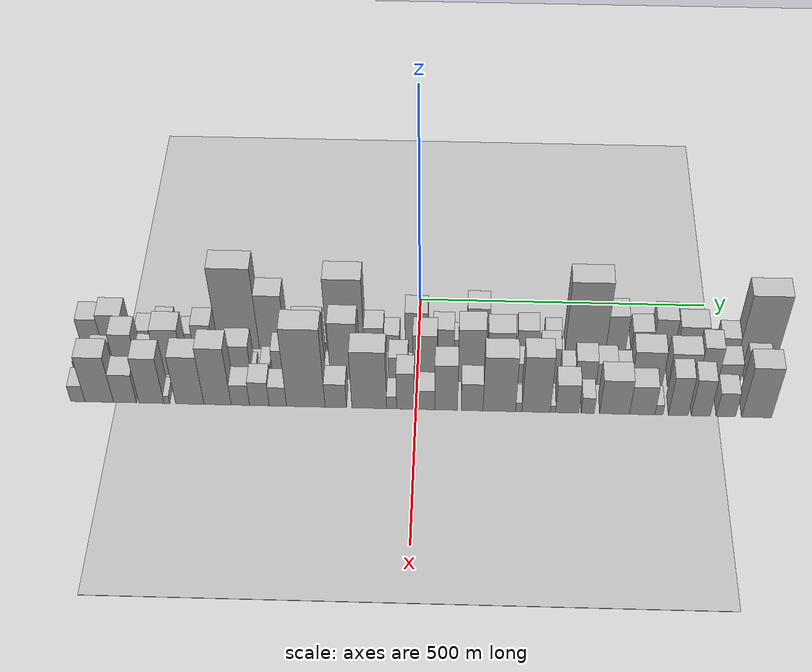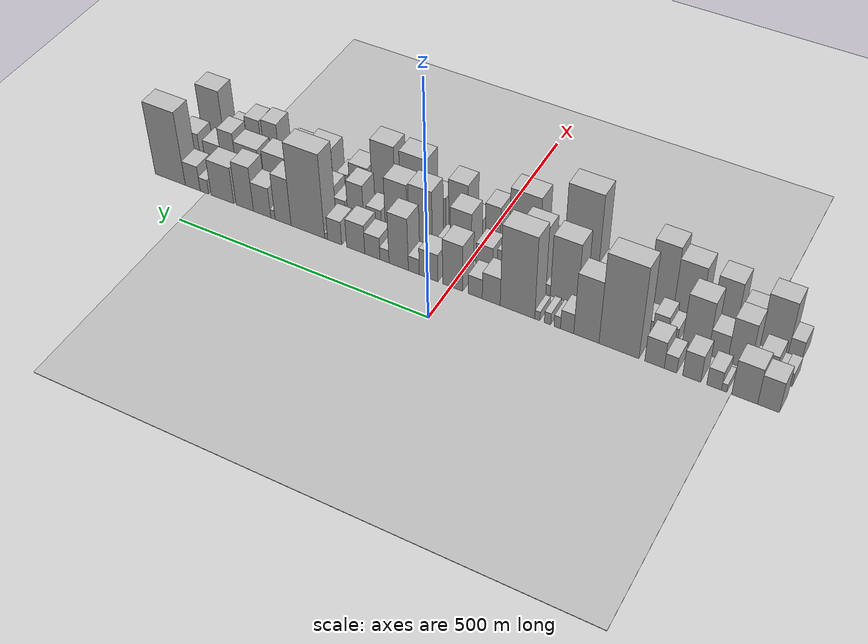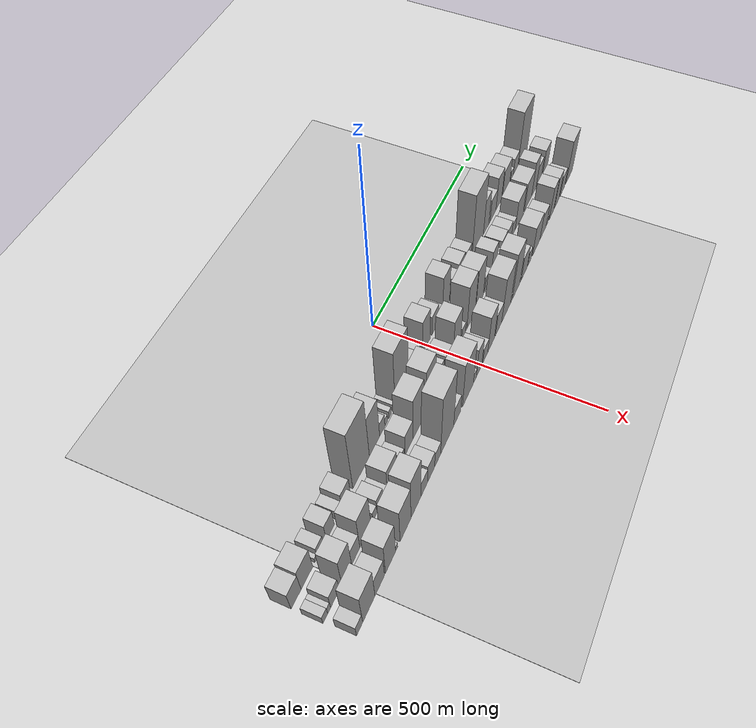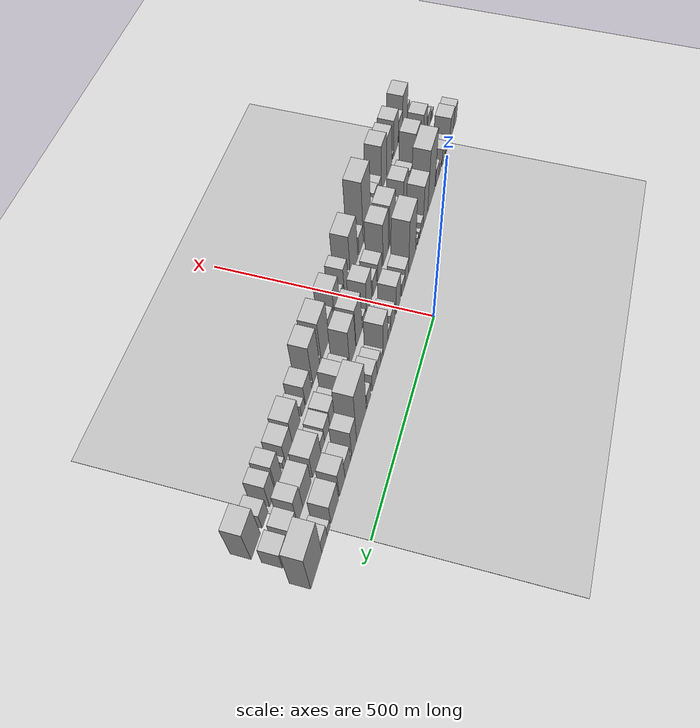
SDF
<?xml version="1.0" encoding="utf-8"?>

<sdf version="1.6">

   <world name="default">

      <gui fullscreen="0">

         <camera name="user_camera">

            <pose>-15 0 4.57585 0 0 0</pose>

            <view_controller>orbit</view_controller>

         </camera>

      </gui>

      <scene>

         <sky>

           <clouds>

             <speed>12</speed>

           </clouds>

         </sky>

         <ambient>0.4 0.4 0.4 1</ambient>

         <background>0.7 0.7 0.7 1</background>

         <shadows>1</shadows>

      </scene>

      <gravity>0 0 -9.8066</gravity>

      <magnetic_field>6e-06 2.3e-05 -4.2e-05</magnetic_field>

      <physics default="0" name="default_physics" type="ode">

         <ode>

            <solver>

               <type>quick</type>

               <iters>10</iters>

               <sor>1.0</sor>

               <use_dynamic_moi_rescaling>0</use_dynamic_moi_rescaling>

            </solver>

            <constraints>

               <cfm>0</cfm>

               <erp>0.2</erp>

               <contact_max_correcting_vel>100</contact_max_correcting_vel>

               <contact_surface_layer>0.001</contact_surface_layer>

            </constraints>

         </ode>

         <max_step_size>0.004</max_step_size>

         <real_time_factor>1</real_time_factor>

         <real_time_update_rate>250</real_time_update_rate>

      </physics>

      <light name="sun" type="directional">

         <cast_shadows>1</cast_shadows>

         <pose>0 0 10 0 0 0</pose>

         <diffuse>0.8 0.8 0.8 1</diffuse>

         <specular>0.2 0.2 0.2 1</specular>

         <attenuation>

            <range>1000</range>

            <constant>0.9</constant>

            <linear>0.01</linear>

            <quadratic>0.001</quadratic>

         </attenuation>

         <direction>-0.5 0.1 -0.9</direction>

      </light>

      <include>

         <name>ground_plane_1</name>

         <uri>model://HANNAS_ground_plane</uri>

         <pose>0 0 0  0 0 0</pose>

      </include>

      <include>

         <name>ground_plane_2</name>

         <uri>model://HANNAS_ground_plane</uri>

         <pose>100 0 0  0 0 0</pose>

      </include>

      <model name="building_1">

         <static>1</static>

         <pose frame="">100.0000 -562.0914 0 0.000000 0.000000 0.000000</pose>

         <link name="link">

            <pose frame="">0 0 34.50 0 0 0</pose>

            <collision name="collision">

               <geometry>

                  <box>

                     <size>40.0000 35.8171 69.0000</size>

                  </box>

               </geometry>

               <max_contacts>10</max_contacts>

               <surface>

                  <contact>

                     <ode/>

                  </contact>

                  <bounce/>

                  <friction>

                     <torsional>

                        <ode/>

                     </torsional>

                     <ode/>

                  </friction>

               </surface>

            </collision>

            <visual name="visual">

               <cast_shadows>0</cast_shadows>

               <geometry>

                  <box>

                     <size>40.0000 35.8171 69.0000</size>

                  </box>

               </geometry>

               <material>

                  <script>

                     <uri>model://HANNAS_wall/materials/scripts</uri>

                     <uri>model://HANNAS_wall/materials/textures</uri>

                     <name>vrc/HANNAS_wall</name>

                  </script>

               </material>

            </visual>

            <self_collide>0</self_collide>

            <enable_wind>0</enable_wind>

            <kinematic>0</kinematic>

         </link>

      </model>

      <model name="building_2">

         <static>1</static>

         <pose frame="">100.0000 -522.6180 0 0.000000 0.000000 0.000000</pose>

         <link name="link">

            <pose frame="">0 0 40.50 0 0 0</pose>

            <collision name="collision">

               <geometry>

                  <box>

                     <size>40.0000 43.1298 81.0000</size>

                  </box>

               </geometry>

               <max_contacts>10</max_contacts>

               <surface>

                  <contact>

                     <ode/>

                  </contact>

                  <bounce/>

                  <friction>

                     <torsional>

                        <ode/>

                     </torsional>

                     <ode/>

                  </friction>

               </surface>

            </collision>

            <visual name="visual">

               <cast_shadows>0</cast_shadows>

               <geometry>

                  <box>

                     <size>40.0000 43.1298 81.0000</size>

                  </box>

               </geometry>

               <material>

                  <script>

                     <uri>model://HANNAS_wall/materials/scripts</uri>

                     <uri>model://HANNAS_wall/materials/textures</uri>

                     <name>vrc/HANNAS_wall</name>

                  </script>

               </material>

            </visual>

            <self_collide>0</self_collide>

            <enable_wind>0</enable_wind>

            <kinematic>0</kinematic>

         </link>

      </model>

      <model name="building_3">

         <static>1</static>

         <pose frame="">100.0000 -488.5580 0 0.000000 0.000000 0.000000</pose>

         <link name="link">

            <pose frame="">0 0 9.00 0 0 0</pose>

            <collision name="collision">

               <geometry>

                  <box>

                     <size>40.0000 8.9903 18.0000</size>

                  </box>

               </geometry>

               <max_contacts>10</max_contacts>

               <surface>

                  <contact>

                     <ode/>

                  </contact>

                  <bounce/>

                  <friction>

                     <torsional>

                        <ode/>

                     </torsional>

                     <ode/>

                  </friction>

               </surface>

            </collision>

            <visual name="visual">

               <cast_shadows>0</cast_shadows>

               <geometry>

                  <box>

                     <size>40.0000 8.9903 18.0000</size>

                  </box>

               </geometry>

               <material>

                  <script>

                     <uri>model://HANNAS_wall/materials/scripts</uri>

                     <uri>model://HANNAS_wall/materials/textures</uri>

                     <name>vrc/HANNAS_wall</name>

                  </script>

               </material>

            </visual>

            <self_collide>0</self_collide>

            <enable_wind>0</enable_wind>

            <kinematic>0</kinematic>

         </link>

      </model>

      <model name="building_4">

         <static>1</static>

         <pose frame="">100.0000 -471.5464 0 0.000000 0.000000 0.000000</pose>

         <link name="link">

            <pose frame="">0 0 21.00 0 0 0</pose>

            <collision name="collision">

               <geometry>

                  <box>

                     <size>40.0000 25.0329 42.0000</size>

                  </box>

               </geometry>

               <max_contacts>10</max_contacts>

               <surface>

                  <contact>

                     <ode/>

                  </contact>

                  <bounce/>

                  <friction>

                     <torsional>

                        <ode/>

                     </torsional>

                     <ode/>

                  </friction>

               </surface>

            </collision>

            <visual name="visual">

               <cast_shadows>0</cast_shadows>

               <geometry>

                  <box>

                     <size>40.0000 25.0329 42.0000</size>

                  </box>

               </geometry>

               <material>

                  <script>

                     <uri>model://HANNAS_wall/materials/scripts</uri>

                     <uri>model://HANNAS_wall/materials/textures</uri>

                     <name>vrc/HANNAS_wall</name>

                  </script>

               </material>

            </visual>

            <self_collide>0</self_collide>

            <enable_wind>0</enable_wind>

            <kinematic>0</kinematic>

         </link>

      </model>

      <model name="building_5">

         <static>1</static>

         <pose frame="">100.0000 -433.6001 0 0.000000 0.000000 0.000000</pose>

         <link name="link">

            <pose frame="">0 0 30.00 0 0 0</pose>

            <collision name="collision">

               <geometry>

                  <box>

                     <size>40.0000 30.8597 60.0000</size>

                  </box>

               </geometry>

               <max_contacts>10</max_contacts>

               <surface>

                  <contact>

                     <ode/>

                  </contact>

                  <bounce/>

                  <friction>

                     <torsional>

                        <ode/>

                     </torsional>

                     <ode/>

                  </friction>

               </surface>

            </collision>

            <visual name="visual">

               <cast_shadows>0</cast_shadows>

               <geometry>

                  <box>

                     <size>40.0000 30.8597 60.0000</size>

                  </box>

               </geometry>

               <material>

                  <script>

                     <uri>model://HANNAS_wall/materials/scripts</uri>

                     <uri>model://HANNAS_wall/materials/textures</uri>

                     <name>vrc/HANNAS_wall</name>

                  </script>

               </material>

            </visual>

            <self_collide>0</self_collide>

            <enable_wind>0</enable_wind>

            <kinematic>0</kinematic>

         </link>

      </model>

      <model name="building_6">

         <static>1</static>

         <pose frame="">100.0000 -397.3919 0 0.000000 0.000000 0.000000</pose>

         <link name="link">

            <pose frame="">0 0 18.00 0 0 0</pose>

            <collision name="collision">

               <geometry>

                  <box>

                     <size>40.0000 21.5565 36.0000</size>

                  </box>

               </geometry>

               <max_contacts>10</max_contacts>

               <surface>

                  <contact>

                     <ode/>

                  </contact>

                  <bounce/>

                  <friction>

                     <torsional>

                        <ode/>

                     </torsional>

                     <ode/>

                  </friction>

               </surface>

            </collision>

            <visual name="visual">

               <cast_shadows>0</cast_shadows>

               <geometry>

                  <box>

                     <size>40.0000 21.5565 36.0000</size>

                  </box>

               </geometry>

               <material>

                  <script>

                     <uri>model://HANNAS_wall/materials/scripts</uri>

                     <uri>model://HANNAS_wall/materials/textures</uri>

                     <name>vrc/HANNAS_wall</name>

                  </script>

               </material>

            </visual>

            <self_collide>0</self_collide>

            <enable_wind>0</enable_wind>

            <kinematic>0</kinematic>

         </link>

      </model>

      <model name="building_7">

         <static>1</static>

         <pose frame="">100.0000 -369.7192 0 0.000000 0.000000 0.000000</pose>

         <link name="link">

            <pose frame="">0 0 30.00 0 0 0</pose>

            <collision name="collision">

               <geometry>

                  <box>

                     <size>40.0000 33.7889 60.0000</size>

                  </box>

               </geometry>

               <max_contacts>10</max_contacts>

               <surface>

                  <contact>

                     <ode/>

                  </contact>

                  <bounce/>

                  <friction>

                     <torsional>

                        <ode/>

                     </torsional>

                     <ode/>

                  </friction>

               </surface>

            </collision>

            <visual name="visual">

               <cast_shadows>0</cast_shadows>

               <geometry>

                  <box>

                     <size>40.0000 33.7889 60.0000</size>

                  </box>

               </geometry>

               <material>

                  <script>

                     <uri>model://HANNAS_wall/materials/scripts</uri>

                     <uri>model://HANNAS_wall/materials/textures</uri>

                     <name>vrc/HANNAS_wall</name>

                  </script>

               </material>

            </visual>

            <self_collide>0</self_collide>

            <enable_wind>0</enable_wind>

            <kinematic>0</kinematic>

         </link>

      </model>

      <model name="building_8">

         <static>1</static>

         <pose frame="">100.0000 -307.5789 0 0.000000 0.000000 0.000000</pose>

         <link name="link">

            <pose frame="">0 0 103.50 0 0 0</pose>

            <collision name="collision">

               <geometry>

                  <box>

                     <size>40.0000 70.4918 207.0000</size>

                  </box>

               </geometry>

               <max_contacts>10</max_contacts>

               <surface>

                  <contact>

                     <ode/>

                  </contact>

                  <bounce/>

                  <friction>

                     <torsional>

                        <ode/>

                     </torsional>

                     <ode/>

                  </friction>

               </surface>

            </collision>

            <visual name="visual">

               <cast_shadows>0</cast_shadows>

               <geometry>

                  <box>

                     <size>40.0000 70.4918 207.0000</size>

                  </box>

               </geometry>

               <material>

                  <script>

                     <uri>model://HANNAS_wall/materials/scripts</uri>

                     <uri>model://HANNAS_wall/materials/textures</uri>

                     <name>vrc/HANNAS_wall</name>

                  </script>

               </material>

            </visual>

            <self_collide>0</self_collide>

            <enable_wind>0</enable_wind>

            <kinematic>0</kinematic>

         </link>

      </model>

      <model name="building_9">

         <static>1</static>

         <pose frame="">100.0000 -249.7459 0 0.000000 0.000000 0.000000</pose>

         <link name="link">

            <pose frame="">0 0 70.50 0 0 0</pose>

            <collision name="collision">

               <geometry>

                  <box>

                     <size>40.0000 45.1742 141.0000</size>

                  </box>

               </geometry>

               <max_contacts>10</max_contacts>

               <surface>

                  <contact>

                     <ode/>

                  </contact>

                  <bounce/>

                  <friction>

                     <torsional>

                        <ode/>

                     </torsional>

                     <ode/>

                  </friction>

               </surface>

            </collision>

            <visual name="visual">

               <cast_shadows>0</cast_shadows>

               <geometry>

                  <box>

                     <size>40.0000 45.1742 141.0000</size>

                  </box>

               </geometry>

               <material>

                  <script>

                     <uri>model://HANNAS_wall/materials/scripts</uri>

                     <uri>model://HANNAS_wall/materials/textures</uri>

                     <name>vrc/HANNAS_wall</name>

                  </script>

               </material>

            </visual>

            <self_collide>0</self_collide>

            <enable_wind>0</enable_wind>

            <kinematic>0</kinematic>

         </link>

      </model>

      <model name="building_10">

         <static>1</static>

         <pose frame="">100.0000 -215.1485 0 0.000000 0.000000 0.000000</pose>

         <link name="link">

            <pose frame="">0 0 22.50 0 0 0</pose>

            <collision name="collision">

               <geometry>

                  <box>

                     <size>40.0000 24.0207 45.0000</size>

                  </box>

               </geometry>

               <max_contacts>10</max_contacts>

               <surface>

                  <contact>

                     <ode/>

                  </contact>

                  <bounce/>

                  <friction>

                     <torsional>

                        <ode/>

                     </torsional>

                     <ode/>

                  </friction>

               </surface>

            </collision>

            <visual name="visual">

               <cast_shadows>0</cast_shadows>

               <geometry>

                  <box>

                     <size>40.0000 24.0207 45.0000</size>

                  </box>

               </geometry>

               <material>

                  <script>

                     <uri>model://HANNAS_wall/materials/scripts</uri>

                     <uri>model://HANNAS_wall/materials/textures</uri>

                     <name>vrc/HANNAS_wall</name>

                  </script>

               </material>

            </visual>

            <self_collide>0</self_collide>

            <enable_wind>0</enable_wind>

            <kinematic>0</kinematic>

         </link>

      </model>

      <model name="building_11">

         <static>1</static>

         <pose frame="">100.0000 -197.2967 0 0.000000 0.000000 0.000000</pose>

         <link name="link">

            <pose frame="">0 0 13.50 0 0 0</pose>

            <collision name="collision">

               <geometry>

                  <box>

                     <size>40.0000 11.6830 27.0000</size>

                  </box>

               </geometry>

               <max_contacts>10</max_contacts>

               <surface>

                  <contact>

                     <ode/>

                  </contact>

                  <bounce/>

                  <friction>

                     <torsional>

                        <ode/>

                     </torsional>

                     <ode/>

                  </friction>

               </surface>

            </collision>

            <visual name="visual">

               <cast_shadows>0</cast_shadows>

               <geometry>

                  <box>

                     <size>40.0000 11.6830 27.0000</size>

                  </box>

               </geometry>

               <material>

                  <script>

                     <uri>model://HANNAS_wall/materials/scripts</uri>

                     <uri>model://HANNAS_wall/materials/textures</uri>

                     <name>vrc/HANNAS_wall</name>

                  </script>

               </material>

            </visual>

            <self_collide>0</self_collide>

            <enable_wind>0</enable_wind>

            <kinematic>0</kinematic>

         </link>

      </model>

      <model name="building_12">

         <static>1</static>

         <pose frame="">100.0000 -179.6461 0 0.000000 0.000000 0.000000</pose>

         <link name="link">

            <pose frame="">0 0 13.50 0 0 0</pose>

            <collision name="collision">

               <geometry>

                  <box>

                     <size>40.0000 11.6181 27.0000</size>

                  </box>

               </geometry>

               <max_contacts>10</max_contacts>

               <surface>

                  <contact>

                     <ode/>

                  </contact>

                  <bounce/>

                  <friction>

                     <torsional>

                        <ode/>

                     </torsional>

                     <ode/>

                  </friction>

               </surface>

            </collision>

            <visual name="visual">

               <cast_shadows>0</cast_shadows>

               <geometry>

                  <box>

                     <size>40.0000 11.6181 27.0000</size>

                  </box>

               </geometry>

               <material>

                  <script>

                     <uri>model://HANNAS_wall/materials/scripts</uri>

                     <uri>model://HANNAS_wall/materials/textures</uri>

                     <name>vrc/HANNAS_wall</name>

                  </script>

               </material>

            </visual>

            <self_collide>0</self_collide>

            <enable_wind>0</enable_wind>

            <kinematic>0</kinematic>

         </link>

      </model>

      <model name="building_13">

         <static>1</static>

         <pose frame="">100.0000 -161.0762 0 0.000000 0.000000 0.000000</pose>

         <link name="link">

            <pose frame="">0 0 10.50 0 0 0</pose>

            <collision name="collision">

               <geometry>

                  <box>

                     <size>40.0000 9.5217 21.0000</size>

                  </box>

               </geometry>

               <max_contacts>10</max_contacts>

               <surface>

                  <contact>

                     <ode/>

                  </contact>

                  <bounce/>

                  <friction>

                     <torsional>

                        <ode/>

                     </torsional>

                     <ode/>

                  </friction>

               </surface>

            </collision>

            <visual name="visual">

               <cast_shadows>0</cast_shadows>

               <geometry>

                  <box>

                     <size>40.0000 9.5217 21.0000</size>

                  </box>

               </geometry>

               <material>

                  <script>

                     <uri>model://HANNAS_wall/materials/scripts</uri>

                     <uri>model://HANNAS_wall/materials/textures</uri>

                     <name>vrc/HANNAS_wall</name>

                  </script>

               </material>

            </visual>

            <self_collide>0</self_collide>

            <enable_wind>0</enable_wind>

            <kinematic>0</kinematic>

         </link>

      </model>

      <model name="building_14">

         <static>1</static>

         <pose frame="">100.0000 -124.3633 0 0.000000 0.000000 0.000000</pose>

         <link name="link">

            <pose frame="">0 0 93.00 0 0 0</pose>

            <collision name="collision">

               <geometry>

                  <box>

                     <size>40.0000 63.9041 186.0000</size>

                  </box>

               </geometry>

               <max_contacts>10</max_contacts>

               <surface>

                  <contact>

                     <ode/>

                  </contact>

                  <bounce/>

                  <friction>

                     <torsional>

                        <ode/>

                     </torsional>

                     <ode/>

                  </friction>

               </surface>

            </collision>

            <visual name="visual">

               <cast_shadows>0</cast_shadows>

               <geometry>

                  <box>

                     <size>40.0000 63.9041 186.0000</size>

                  </box>

               </geometry>

               <material>

                  <script>

                     <uri>model://HANNAS_wall/materials/scripts</uri>

                     <uri>model://HANNAS_wall/materials/textures</uri>

                     <name>vrc/HANNAS_wall</name>

                  </script>

               </material>

            </visual>

            <self_collide>0</self_collide>

            <enable_wind>0</enable_wind>

            <kinematic>0</kinematic>

         </link>

      </model>

      <model name="building_15">

         <static>1</static>

         <pose frame="">100.0000 -75.5403 0 0.000000 0.000000 0.000000</pose>

         <link name="link">

            <pose frame="">0 0 31.50 0 0 0</pose>

            <collision name="collision">

               <geometry>

                  <box>

                     <size>40.0000 33.7419 63.0000</size>

                  </box>

               </geometry>

               <max_contacts>10</max_contacts>

               <surface>

                  <contact>

                     <ode/>

                  </contact>

                  <bounce/>

                  <friction>

                     <torsional>

                        <ode/>

                     </torsional>

                     <ode/>

                  </friction>

               </surface>

            </collision>

            <visual name="visual">

               <cast_shadows>0</cast_shadows>

               <geometry>

                  <box>

                     <size>40.0000 33.7419 63.0000</size>

                  </box>

               </geometry>

               <material>

                  <script>

                     <uri>model://HANNAS_wall/materials/scripts</uri>

                     <uri>model://HANNAS_wall/materials/textures</uri>

                     <name>vrc/HANNAS_wall</name>

                  </script>

               </material>

            </visual>

            <self_collide>0</self_collide>

            <enable_wind>0</enable_wind>

            <kinematic>0</kinematic>

         </link>

      </model>

      <model name="building_16">

         <static>1</static>

         <pose frame="">100.0000 -45.2591 0 0.000000 0.000000 0.000000</pose>

         <link name="link">

            <pose frame="">0 0 22.50 0 0 0</pose>

            <collision name="collision">

               <geometry>

                  <box>

                     <size>40.0000 26.8206 45.0000</size>

                  </box>

               </geometry>

               <max_contacts>10</max_contacts>

               <surface>

                  <contact>

                     <ode/>

                  </contact>

                  <bounce/>

                  <friction>

                     <torsional>

                        <ode/>

                     </torsional>

                     <ode/>

                  </friction>

               </surface>

            </collision>

            <visual name="visual">

               <cast_shadows>0</cast_shadows>

               <geometry>

                  <box>

                     <size>40.0000 26.8206 45.0000</size>

                  </box>

               </geometry>

               <material>

                  <script>

                     <uri>model://HANNAS_wall/materials/scripts</uri>

                     <uri>model://HANNAS_wall/materials/textures</uri>

                     <name>vrc/HANNAS_wall</name>

                  </script>

               </material>

            </visual>

            <self_collide>0</self_collide>

            <enable_wind>0</enable_wind>

            <kinematic>0</kinematic>

         </link>

      </model>

      <model name="building_17">

         <static>1</static>

         <pose frame="">100.0000 -2.6604 0 0.000000 0.000000 0.000000</pose>

         <link name="link">

            <pose frame="">0 0 52.50 0 0 0</pose>

            <collision name="collision">

               <geometry>

                  <box>

                     <size>40.0000 38.3768 105.0000</size>

                  </box>

               </geometry>

               <max_contacts>10</max_contacts>

               <surface>

                  <contact>

                     <ode/>

                  </contact>

                  <bounce/>

                  <friction>

                     <torsional>

                        <ode/>

                     </torsional>

                     <ode/>

                  </friction>

               </surface>

            </collision>

            <visual name="visual">

               <cast_shadows>0</cast_shadows>

               <geometry>

                  <box>

                     <size>40.0000 38.3768 105.0000</size>

                  </box>

               </geometry>

               <material>

                  <script>

                     <uri>model://HANNAS_wall/materials/scripts</uri>

                     <uri>model://HANNAS_wall/materials/textures</uri>

                     <name>vrc/HANNAS_wall</name>

                  </script>

               </material>

            </visual>

            <self_collide>0</self_collide>

            <enable_wind>0</enable_wind>

            <kinematic>0</kinematic>

         </link>

      </model>

      <model name="building_18">

         <static>1</static>

         <pose frame="">100.0000 43.6030 0 0.000000 0.000000 0.000000</pose>

         <link name="link">

            <pose frame="">0 0 31.50 0 0 0</pose>

            <collision name="collision">

               <geometry>

                  <box>

                     <size>40.0000 36.1499 63.0000</size>

                  </box>

               </geometry>

               <max_contacts>10</max_contacts>

               <surface>

                  <contact>

                     <ode/>

                  </contact>

                  <bounce/>

                  <friction>

                     <torsional>

                        <ode/>

                     </torsional>

                     <ode/>

                  </friction>

               </surface>

            </collision>

            <visual name="visual">

               <cast_shadows>0</cast_shadows>

               <geometry>

                  <box>

                     <size>40.0000 36.1499 63.0000</size>

                  </box>

               </geometry>

               <material>

                  <script>

                     <uri>model://HANNAS_wall/materials/scripts</uri>

                     <uri>model://HANNAS_wall/materials/textures</uri>

                     <name>vrc/HANNAS_wall</name>

                  </script>

               </material>

            </visual>

            <self_collide>0</self_collide>

            <enable_wind>0</enable_wind>

            <kinematic>0</kinematic>

         </link>

      </model>

      <model name="building_19">

         <static>1</static>

         <pose frame="">100.0000 72.2824 0 0.000000 0.000000 0.000000</pose>

         <link name="link">

            <pose frame="">0 0 18.00 0 0 0</pose>

            <collision name="collision">

               <geometry>

                  <box>

                     <size>40.0000 21.2088 36.0000</size>

                  </box>

               </geometry>

               <max_contacts>10</max_contacts>

               <surface>

                  <contact>

                     <ode/>

                  </contact>

                  <bounce/>

                  <friction>

                     <torsional>

                        <ode/>

                     </torsional>

                     <ode/>

                  </friction>

               </surface>

            </collision>

            <visual name="visual">

               <cast_shadows>0</cast_shadows>

               <geometry>

                  <box>

                     <size>40.0000 21.2088 36.0000</size>

                  </box>

               </geometry>

               <material>

                  <script>

                     <uri>model://HANNAS_wall/materials/scripts</uri>

                     <uri>model://HANNAS_wall/materials/textures</uri>

                     <name>vrc/HANNAS_wall</name>

                  </script>

               </material>

            </visual>

            <self_collide>0</self_collide>

            <enable_wind>0</enable_wind>

            <kinematic>0</kinematic>

         </link>

      </model>

      <model name="building_20">

         <static>1</static>

         <pose frame="">100.0000 101.8695 0 0.000000 0.000000 0.000000</pose>

         <link name="link">

            <pose frame="">0 0 60.00 0 0 0</pose>

            <collision name="collision">

               <geometry>

                  <box>

                     <size>40.0000 37.9655 120.0000</size>

                  </box>

               </geometry>

               <max_contacts>10</max_contacts>

               <surface>

                  <contact>

                     <ode/>

                  </contact>

                  <bounce/>

                  <friction>

                     <torsional>

                        <ode/>

                     </torsional>

                     <ode/>

                  </friction>

               </surface>

            </collision>

            <visual name="visual">

               <cast_shadows>0</cast_shadows>

               <geometry>

                  <box>

                     <size>40.0000 37.9655 120.0000</size>

                  </box>

               </geometry>

               <material>

                  <script>

                     <uri>model://HANNAS_wall/materials/scripts</uri>

                     <uri>model://HANNAS_wall/materials/textures</uri>

                     <name>vrc/HANNAS_wall</name>

                  </script>

               </material>

            </visual>

            <self_collide>0</self_collide>

            <enable_wind>0</enable_wind>

            <kinematic>0</kinematic>

         </link>

      </model>

      <model name="building_21">

         <static>1</static>

         <pose frame="">100.0000 129.8456 0 0.000000 0.000000 0.000000</pose>

         <link name="link">

            <pose frame="">0 0 15.00 0 0 0</pose>

            <collision name="collision">

               <geometry>

                  <box>

                     <size>40.0000 17.9866 30.0000</size>

                  </box>

               </geometry>

               <max_contacts>10</max_contacts>

               <surface>

                  <contact>

                     <ode/>

                  </contact>

                  <bounce/>

                  <friction>

                     <torsional>

                        <ode/>

                     </torsional>

                     <ode/>

                  </friction>

               </surface>

            </collision>

            <visual name="visual">

               <cast_shadows>0</cast_shadows>

               <geometry>

                  <box>

                     <size>40.0000 17.9866 30.0000</size>

                  </box>

               </geometry>

               <material>

                  <script>

                     <uri>model://HANNAS_wall/materials/scripts</uri>

                     <uri>model://HANNAS_wall/materials/textures</uri>

                     <name>vrc/HANNAS_wall</name>

                  </script>

               </material>

            </visual>

            <self_collide>0</self_collide>

            <enable_wind>0</enable_wind>

            <kinematic>0</kinematic>

         </link>

      </model>

      <model name="building_22">

         <static>1</static>

         <pose frame="">100.0000 153.8802 0 0.000000 0.000000 0.000000</pose>

         <link name="link">

            <pose frame="">0 0 25.50 0 0 0</pose>

            <collision name="collision">

               <geometry>

                  <box>

                     <size>40.0000 30.0826 51.0000</size>

                  </box>

               </geometry>

               <max_contacts>10</max_contacts>

               <surface>

                  <contact>

                     <ode/>

                  </contact>

                  <bounce/>

                  <friction>

                     <torsional>

                        <ode/>

                     </torsional>

                     <ode/>

                  </friction>

               </surface>

            </collision>

            <visual name="visual">

               <cast_shadows>0</cast_shadows>

               <geometry>

                  <box>

                     <size>40.0000 30.0826 51.0000</size>

                  </box>

               </geometry>

               <material>

                  <script>

                     <uri>model://HANNAS_wall/materials/scripts</uri>

                     <uri>model://HANNAS_wall/materials/textures</uri>

                     <name>vrc/HANNAS_wall</name>

                  </script>

               </material>

            </visual>

            <self_collide>0</self_collide>

            <enable_wind>0</enable_wind>

            <kinematic>0</kinematic>

         </link>

      </model>

      <model name="building_23">

         <static>1</static>

         <pose frame="">100.0000 187.1599 0 0.000000 0.000000 0.000000</pose>

         <link name="link">

            <pose frame="">0 0 33.00 0 0 0</pose>

            <collision name="collision">

               <geometry>

                  <box>

                     <size>40.0000 36.4768 66.0000</size>

                  </box>

               </geometry>

               <max_contacts>10</max_contacts>

               <surface>

                  <contact>

                     <ode/>

                  </contact>

                  <bounce/>

                  <friction>

                     <torsional>

                        <ode/>

                     </torsional>

                     <ode/>

                  </friction>

               </surface>

            </collision>

            <visual name="visual">

               <cast_shadows>0</cast_shadows>

               <geometry>

                  <box>

                     <size>40.0000 36.4768 66.0000</size>

                  </box>

               </geometry>

               <material>

                  <script>

                     <uri>model://HANNAS_wall/materials/scripts</uri>

                     <uri>model://HANNAS_wall/materials/textures</uri>

                     <name>vrc/HANNAS_wall</name>

                  </script>

               </material>

            </visual>

            <self_collide>0</self_collide>

            <enable_wind>0</enable_wind>

            <kinematic>0</kinematic>

         </link>

      </model>

      <model name="building_24">

         <static>1</static>

         <pose frame="">100.0000 229.6737 0 0.000000 0.000000 0.000000</pose>

         <link name="link">

            <pose frame="">0 0 27.00 0 0 0</pose>

            <collision name="collision">

               <geometry>

                  <box>

                     <size>40.0000 28.5508 54.0000</size>

                  </box>

               </geometry>

               <max_contacts>10</max_contacts>

               <surface>

                  <contact>

                     <ode/>

                  </contact>

                  <bounce/>

                  <friction>

                     <torsional>

                        <ode/>

                     </torsional>

                     <ode/>

                  </friction>

               </surface>

            </collision>

            <visual name="visual">

               <cast_shadows>0</cast_shadows>

               <geometry>

                  <box>

                     <size>40.0000 28.5508 54.0000</size>

                  </box>

               </geometry>

               <material>

                  <script>

                     <uri>model://HANNAS_wall/materials/scripts</uri>

                     <uri>model://HANNAS_wall/materials/textures</uri>

                     <name>vrc/HANNAS_wall</name>

                  </script>

               </material>

            </visual>

            <self_collide>0</self_collide>

            <enable_wind>0</enable_wind>

            <kinematic>0</kinematic>

         </link>

      </model>

      <model name="building_25">

         <static>1</static>

         <pose frame="">100.0000 247.0251 0 0.000000 0.000000 0.000000</pose>

         <link name="link">

            <pose frame="">0 0 7.50 0 0 0</pose>

            <collision name="collision">

               <geometry>

                  <box>

                     <size>40.0000 6.1520 15.0000</size>

                  </box>

               </geometry>

               <max_contacts>10</max_contacts>

               <surface>

                  <contact>

                     <ode/>

                  </contact>

                  <bounce/>

                  <friction>

                     <torsional>

                        <ode/>

                     </torsional>

                     <ode/>

                  </friction>

               </surface>

            </collision>

            <visual name="visual">

               <cast_shadows>0</cast_shadows>

               <geometry>

                  <box>

                     <size>40.0000 6.1520 15.0000</size>

                  </box>

               </geometry>

               <material>

                  <script>

                     <uri>model://HANNAS_wall/materials/scripts</uri>

                     <uri>model://HANNAS_wall/materials/textures</uri>

                     <name>vrc/HANNAS_wall</name>

                  </script>

               </material>

            </visual>

            <self_collide>0</self_collide>

            <enable_wind>0</enable_wind>

            <kinematic>0</kinematic>

         </link>

      </model>

      <model name="building_26">

         <static>1</static>

         <pose frame="">100.0000 284.4919 0 0.000000 0.000000 0.000000</pose>

         <link name="link">

            <pose frame="">0 0 96.00 0 0 0</pose>

            <collision name="collision">

               <geometry>

                  <box>

                     <size>40.0000 68.7816 192.0000</size>

                  </box>

               </geometry>

               <max_contacts>10</max_contacts>

               <surface>

                  <contact>

                     <ode/>

                  </contact>

                  <bounce/>

                  <friction>

                     <torsional>

                        <ode/>

                     </torsional>

                     <ode/>

                  </friction>

               </surface>

            </collision>

            <visual name="visual">

               <cast_shadows>0</cast_shadows>

               <geometry>

                  <box>

                     <size>40.0000 68.7816 192.0000</size>

                  </box>

               </geometry>

               <material>

                  <script>

                     <uri>model://HANNAS_wall/materials/scripts</uri>

                     <uri>model://HANNAS_wall/materials/textures</uri>

                     <name>vrc/HANNAS_wall</name>

                  </script>

               </material>

            </visual>

            <self_collide>0</self_collide>

            <enable_wind>0</enable_wind>

            <kinematic>0</kinematic>

         </link>

      </model>

      <model name="building_27">

         <static>1</static>

         <pose frame="">100.0000 335.6351 0 0.000000 0.000000 0.000000</pose>

         <link name="link">

            <pose frame="">0 0 54.00 0 0 0</pose>

            <collision name="collision">

               <geometry>

                  <box>

                     <size>40.0000 33.5049 108.0000</size>

                  </box>

               </geometry>

               <max_contacts>10</max_contacts>

               <surface>

                  <contact>

                     <ode/>

                  </contact>

                  <bounce/>

                  <friction>

                     <torsional>

                        <ode/>

                     </torsional>

                     <ode/>

                  </friction>

               </surface>

            </collision>

            <visual name="visual">

               <cast_shadows>0</cast_shadows>

               <geometry>

                  <box>

                     <size>40.0000 33.5049 108.0000</size>

                  </box>

               </geometry>

               <material>

                  <script>

                     <uri>model://HANNAS_wall/materials/scripts</uri>

                     <uri>model://HANNAS_wall/materials/textures</uri>

                     <name>vrc/HANNAS_wall</name>

                  </script>

               </material>

            </visual>

            <self_collide>0</self_collide>

            <enable_wind>0</enable_wind>

            <kinematic>0</kinematic>

         </link>

      </model>

      <model name="building_28">

         <static>1</static>

         <pose frame="">100.0000 356.8194 0 0.000000 0.000000 0.000000</pose>

         <link name="link">

            <pose frame="">0 0 10.50 0 0 0</pose>

            <collision name="collision">

               <geometry>

                  <box>

                     <size>40.0000 8.8637 21.0000</size>

                  </box>

               </geometry>

               <max_contacts>10</max_contacts>

               <surface>

                  <contact>

                     <ode/>

                  </contact>

                  <bounce/>

                  <friction>

                     <torsional>

                        <ode/>

                     </torsional>

                     <ode/>

                  </friction>

               </surface>

            </collision>

            <visual name="visual">

               <cast_shadows>0</cast_shadows>

               <geometry>

                  <box>

                     <size>40.0000 8.8637 21.0000</size>

                  </box>

               </geometry>

               <material>

                  <script>

                     <uri>model://HANNAS_wall/materials/scripts</uri>

                     <uri>model://HANNAS_wall/materials/textures</uri>

                     <name>vrc/HANNAS_wall</name>

                  </script>

               </material>

            </visual>

            <self_collide>0</self_collide>

            <enable_wind>0</enable_wind>

            <kinematic>0</kinematic>

         </link>

      </model>

      <model name="building_29">

         <static>1</static>

         <pose frame="">100.0000 379.5728 0 0.000000 0.000000 0.000000</pose>

         <link name="link">

            <pose frame="">0 0 34.50 0 0 0</pose>

            <collision name="collision">

               <geometry>

                  <box>

                     <size>40.0000 36.6431 69.0000</size>

                  </box>

               </geometry>

               <max_contacts>10</max_contacts>

               <surface>

                  <contact>

                     <ode/>

                  </contact>

                  <bounce/>

                  <friction>

                     <torsional>

                        <ode/>

                     </torsional>

                     <ode/>

                  </friction>

               </surface>

            </collision>

            <visual name="visual">

               <cast_shadows>0</cast_shadows>

               <geometry>

                  <box>

                     <size>40.0000 36.6431 69.0000</size>

                  </box>

               </geometry>

               <material>

                  <script>

                     <uri>model://HANNAS_wall/materials/scripts</uri>

                     <uri>model://HANNAS_wall/materials/textures</uri>

                     <name>vrc/HANNAS_wall</name>

                  </script>

               </material>

            </visual>

            <self_collide>0</self_collide>

            <enable_wind>0</enable_wind>

            <kinematic>0</kinematic>

         </link>

      </model>

      <model name="building_30">

         <static>1</static>

         <pose frame="">100.0000 416.3446 0 0.000000 0.000000 0.000000</pose>

         <link name="link">

            <pose frame="">0 0 51.00 0 0 0</pose>

            <collision name="collision">

               <geometry>

                  <box>

                     <size>40.0000 36.9004 102.0000</size>

                  </box>

               </geometry>

               <max_contacts>10</max_contacts>

               <surface>

                  <contact>

                     <ode/>

                  </contact>

                  <bounce/>

                  <friction>

                     <torsional>

                        <ode/>

                     </torsional>

                     <ode/>

                  </friction>

               </surface>

            </collision>

            <visual name="visual">

               <cast_shadows>0</cast_shadows>

               <geometry>

                  <box>

                     <size>40.0000 36.9004 102.0000</size>

                  </box>

               </geometry>

               <material>

                  <script>

                     <uri>model://HANNAS_wall/materials/scripts</uri>

                     <uri>model://HANNAS_wall/materials/textures</uri>

                     <name>vrc/HANNAS_wall</name>

                  </script>

               </material>

            </visual>

            <self_collide>0</self_collide>

            <enable_wind>0</enable_wind>

            <kinematic>0</kinematic>

         </link>

      </model>

      <model name="building_31">

         <static>1</static>

         <pose frame="">100.0000 464.2166 0 0.000000 0.000000 0.000000</pose>

         <link name="link">

            <pose frame="">0 0 42.00 0 0 0</pose>

            <collision name="collision">

               <geometry>

                  <box>

                     <size>40.0000 48.8437 84.0000</size>

                  </box>

               </geometry>

               <max_contacts>10</max_contacts>

               <surface>

                  <contact>

                     <ode/>

                  </contact>

                  <bounce/>

                  <friction>

                     <torsional>

                        <ode/>

                     </torsional>

                     <ode/>

                  </friction>

               </surface>

            </collision>

            <visual name="visual">

               <cast_shadows>0</cast_shadows>

               <geometry>

                  <box>

                     <size>40.0000 48.8437 84.0000</size>

                  </box>

               </geometry>

               <material>

                  <script>

                     <uri>model://HANNAS_wall/materials/scripts</uri>

                     <uri>model://HANNAS_wall/materials/textures</uri>

                     <name>vrc/HANNAS_wall</name>

                  </script>

               </material>

            </visual>

            <self_collide>0</self_collide>

            <enable_wind>0</enable_wind>

            <kinematic>0</kinematic>

         </link>

      </model>

      <model name="building_32">

         <static>1</static>

         <pose frame="">100.0000 502.9277 0 0.000000 0.000000 0.000000</pose>

         <link name="link">

            <pose frame="">0 0 16.50 0 0 0</pose>

            <collision name="collision">

               <geometry>

                  <box>

                     <size>40.0000 18.5784 33.0000</size>

                  </box>

               </geometry>

               <max_contacts>10</max_contacts>

               <surface>

                  <contact>

                     <ode/>

                  </contact>

                  <bounce/>

                  <friction>

                     <torsional>

                        <ode/>

                     </torsional>

                     <ode/>

                  </friction>

               </surface>

            </collision>

            <visual name="visual">

               <cast_shadows>0</cast_shadows>

               <geometry>

                  <box>

                     <size>40.0000 18.5784 33.0000</size>

                  </box>

               </geometry>

               <material>

                  <script>

                     <uri>model://HANNAS_wall/materials/scripts</uri>

                     <uri>model://HANNAS_wall/materials/textures</uri>

                     <name>vrc/HANNAS_wall</name>

                  </script>

               </material>

            </visual>

            <self_collide>0</self_collide>

            <enable_wind>0</enable_wind>

            <kinematic>0</kinematic>

         </link>

      </model>

      <model name="building_33">

         <static>1</static>

         <pose frame="">100.0000 528.4617 0 0.000000 0.000000 0.000000</pose>

         <link name="link">

            <pose frame="">0 0 28.50 0 0 0</pose>

            <collision name="collision">

               <geometry>

                  <box>

                     <size>40.0000 32.4897 57.0000</size>

                  </box>

               </geometry>

               <max_contacts>10</max_contacts>

               <surface>

                  <contact>

                     <ode/>

                  </contact>

                  <bounce/>

                  <friction>

                     <torsional>

                        <ode/>

                     </torsional>

                     <ode/>

                  </friction>

               </surface>

            </collision>

            <visual name="visual">

               <cast_shadows>0</cast_shadows>

               <geometry>

                  <box>

                     <size>40.0000 32.4897 57.0000</size>

                  </box>

               </geometry>

               <material>

                  <script>

                     <uri>model://HANNAS_wall/materials/scripts</uri>

                     <uri>model://HANNAS_wall/materials/textures</uri>

                     <name>vrc/HANNAS_wall</name>

                  </script>

               </material>

            </visual>

            <self_collide>0</self_collide>

            <enable_wind>0</enable_wind>

            <kinematic>0</kinematic>

         </link>

      </model>

      <model name="building_34">

         <static>1</static>

         <pose frame="">100.0000 577.9212 0 0.000000 0.000000 0.000000</pose>

         <link name="link">

            <pose frame="">0 0 84.00 0 0 0</pose>

            <collision name="collision">

               <geometry>

                  <box>

                     <size>40.0000 66.4292 168.0000</size>

                  </box>

               </geometry>

               <max_contacts>10</max_contacts>

               <surface>

                  <contact>

                     <ode/>

                  </contact>

                  <bounce/>

                  <friction>

                     <torsional>

                        <ode/>

                     </torsional>

                     <ode/>

                  </friction>

               </surface>

            </collision>

            <visual name="visual">

               <cast_shadows>0</cast_shadows>

               <geometry>

                  <box>

                     <size>40.0000 66.4292 168.0000</size>

                  </box>

               </geometry>

               <material>

                  <script>

                     <uri>model://HANNAS_wall/materials/scripts</uri>

                     <uri>model://HANNAS_wall/materials/textures</uri>

                     <name>vrc/HANNAS_wall</name>

                  </script>

               </material>

            </visual>

            <self_collide>0</self_collide>

            <enable_wind>0</enable_wind>

            <kinematic>0</kinematic>

         </link>

      </model>

      <model name="building_35">

         <static>1</static>

         <pose frame="">160.0000 -571.2576 0 0.000000 0.000000 0.000000</pose>

         <link name="link">

            <pose frame="">0 0 15.00 0 0 0</pose>

            <collision name="collision">

               <geometry>

                  <box>

                     <size>40.0000 17.4849 30.0000</size>

                  </box>

               </geometry>

               <max_contacts>10</max_contacts>

               <surface>

                  <contact>

                     <ode/>

                  </contact>

                  <bounce/>

                  <friction>

                     <torsional>

                        <ode/>

                     </torsional>

                     <ode/>

                  </friction>

               </surface>

            </collision>

            <visual name="visual">

               <cast_shadows>0</cast_shadows>

               <geometry>

                  <box>

                     <size>40.0000 17.4849 30.0000</size>

                  </box>

               </geometry>

               <material>

                  <script>

                     <uri>model://HANNAS_wall/materials/scripts</uri>

                     <uri>model://HANNAS_wall/materials/textures</uri>

                     <name>vrc/HANNAS_wall</name>

                  </script>

               </material>

            </visual>

            <self_collide>0</self_collide>

            <enable_wind>0</enable_wind>

            <kinematic>0</kinematic>

         </link>

      </model>

      <model name="building_36">

         <static>1</static>

         <pose frame="">160.0000 -557.1027 0 0.000000 0.000000 0.000000</pose>

         <link name="link">

            <pose frame="">0 0 13.50 0 0 0</pose>

            <collision name="collision">

               <geometry>

                  <box>

                     <size>40.0000 10.8249 27.0000</size>

                  </box>

               </geometry>

               <max_contacts>10</max_contacts>

               <surface>

                  <contact>

                     <ode/>

                  </contact>

                  <bounce/>

                  <friction>

                     <torsional>

                        <ode/>

                     </torsional>

                     <ode/>

                  </friction>

               </surface>

            </collision>

            <visual name="visual">

               <cast_shadows>0</cast_shadows>

               <geometry>

                  <box>

                     <size>40.0000 10.8249 27.0000</size>

                  </box>

               </geometry>

               <material>

                  <script>

                     <uri>model://HANNAS_wall/materials/scripts</uri>

                     <uri>model://HANNAS_wall/materials/textures</uri>

                     <name>vrc/HANNAS_wall</name>

                  </script>

               </material>

            </visual>

            <self_collide>0</self_collide>

            <enable_wind>0</enable_wind>

            <kinematic>0</kinematic>

         </link>

      </model>

      <model name="building_37">

         <static>1</static>

         <pose frame="">160.0000 -535.5196 0 0.000000 0.000000 0.000000</pose>

         <link name="link">

            <pose frame="">0 0 27.00 0 0 0</pose>

            <collision name="collision">

               <geometry>

                  <box>

                     <size>40.0000 32.3412 54.0000</size>

                  </box>

               </geometry>

               <max_contacts>10</max_contacts>

               <surface>

                  <contact>

                     <ode/>

                  </contact>

                  <bounce/>

                  <friction>

                     <torsional>

                        <ode/>

                     </torsional>

                     <ode/>

                  </friction>

               </surface>

            </collision>

            <visual name="visual">

               <cast_shadows>0</cast_shadows>

               <geometry>

                  <box>

                     <size>40.0000 32.3412 54.0000</size>

                  </box>

               </geometry>

               <material>

                  <script>

                     <uri>model://HANNAS_wall/materials/scripts</uri>

                     <uri>model://HANNAS_wall/materials/textures</uri>

                     <name>vrc/HANNAS_wall</name>

                  </script>

               </material>

            </visual>

            <self_collide>0</self_collide>

            <enable_wind>0</enable_wind>

            <kinematic>0</kinematic>

         </link>

      </model>

      <model name="building_38">

         <static>1</static>

         <pose frame="">160.0000 -490.2751 0 0.000000 0.000000 0.000000</pose>

         <link name="link">

            <pose frame="">0 0 52.50 0 0 0</pose>

            <collision name="collision">

               <geometry>

                  <box>

                     <size>40.0000 38.1479 105.0000</size>

                  </box>

               </geometry>

               <max_contacts>10</max_contacts>

               <surface>

                  <contact>

                     <ode/>

                  </contact>

                  <bounce/>

                  <friction>

                     <torsional>

                        <ode/>

                     </torsional>

                     <ode/>

                  </friction>

               </surface>

            </collision>

            <visual name="visual">

               <cast_shadows>0</cast_shadows>

               <geometry>

                  <box>

                     <size>40.0000 38.1479 105.0000</size>

                  </box>

               </geometry>

               <material>

                  <script>

                     <uri>model://HANNAS_wall/materials/scripts</uri>

                     <uri>model://HANNAS_wall/materials/textures</uri>

                     <name>vrc/HANNAS_wall</name>

                  </script>

               </material>

            </visual>

            <self_collide>0</self_collide>

            <enable_wind>0</enable_wind>

            <kinematic>0</kinematic>

         </link>

      </model>

      <model name="building_39">

         <static>1</static>

         <pose frame="">160.0000 -454.6785 0 0.000000 0.000000 0.000000</pose>

         <link name="link">

            <pose frame="">0 0 30.00 0 0 0</pose>

            <collision name="collision">

               <geometry>

                  <box>

                     <size>40.0000 33.0453 60.0000</size>

                  </box>

               </geometry>

               <max_contacts>10</max_contacts>

               <surface>

                  <contact>

                     <ode/>

                  </contact>

                  <bounce/>

                  <friction>

                     <torsional>

                        <ode/>

                     </torsional>

                     <ode/>

                  </friction>

               </surface>

            </collision>

            <visual name="visual">

               <cast_shadows>0</cast_shadows>

               <geometry>

                  <box>

                     <size>40.0000 33.0453 60.0000</size>

                  </box>

               </geometry>

               <material>

                  <script>

                     <uri>model://HANNAS_wall/materials/scripts</uri>

                     <uri>model://HANNAS_wall/materials/textures</uri>

                     <name>vrc/HANNAS_wall</name>

                  </script>

               </material>

            </visual>

            <self_collide>0</self_collide>

            <enable_wind>0</enable_wind>

            <kinematic>0</kinematic>

         </link>

      </model>

      <model name="building_40">

         <static>1</static>

         <pose frame="">160.0000 -415.4418 0 0.000000 0.000000 0.000000</pose>

         <link name="link">

            <pose frame="">0 0 60.00 0 0 0</pose>

            <collision name="collision">

               <geometry>

                  <box>

                     <size>40.0000 45.4279 120.0000</size>

                  </box>

               </geometry>

               <max_contacts>10</max_contacts>

               <surface>

                  <contact>

                     <ode/>

                  </contact>

                  <bounce/>

                  <friction>

                     <torsional>

                        <ode/>

                     </torsional>

                     <ode/>

                  </friction>

               </surface>

            </collision>

            <visual name="visual">

               <cast_shadows>0</cast_shadows>

               <geometry>

                  <box>

                     <size>40.0000 45.4279 120.0000</size>

                  </box>

               </geometry>

               <material>

                  <script>

                     <uri>model://HANNAS_wall/materials/scripts</uri>

                     <uri>model://HANNAS_wall/materials/textures</uri>

                     <name>vrc/HANNAS_wall</name>

                  </script>

               </material>

            </visual>

            <self_collide>0</self_collide>

            <enable_wind>0</enable_wind>

            <kinematic>0</kinematic>

         </link>

      </model>

      <model name="building_41">

         <static>1</static>

         <pose frame="">160.0000 -376.0880 0 0.000000 0.000000 0.000000</pose>

         <link name="link">

            <pose frame="">0 0 16.50 0 0 0</pose>

            <collision name="collision">

               <geometry>

                  <box>

                     <size>40.0000 17.2798 33.0000</size>

                  </box>

               </geometry>

               <max_contacts>10</max_contacts>

               <surface>

                  <contact>

                     <ode/>

                  </contact>

                  <bounce/>

                  <friction>

                     <torsional>

                        <ode/>

                     </torsional>

                     <ode/>

                  </friction>

               </surface>

            </collision>

            <visual name="visual">

               <cast_shadows>0</cast_shadows>

               <geometry>

                  <box>

                     <size>40.0000 17.2798 33.0000</size>

                  </box>

               </geometry>

               <material>

                  <script>

                     <uri>model://HANNAS_wall/materials/scripts</uri>

                     <uri>model://HANNAS_wall/materials/textures</uri>

                     <name>vrc/HANNAS_wall</name>

                  </script>

               </material>

            </visual>

            <self_collide>0</self_collide>

            <enable_wind>0</enable_wind>

            <kinematic>0</kinematic>

         </link>

      </model>

      <model name="building_42">

         <static>1</static>

         <pose frame="">160.0000 -354.3526 0 0.000000 0.000000 0.000000</pose>

         <link name="link">

            <pose frame="">0 0 25.50 0 0 0</pose>

            <collision name="collision">

               <geometry>

                  <box>

                     <size>40.0000 26.1909 51.0000</size>

                  </box>

               </geometry>

               <max_contacts>10</max_contacts>

               <surface>

                  <contact>

                     <ode/>

                  </contact>

                  <bounce/>

                  <friction>

                     <torsional>

                        <ode/>

                     </torsional>

                     <ode/>

                  </friction>

               </surface>

            </collision>

            <visual name="visual">

               <cast_shadows>0</cast_shadows>

               <geometry>

                  <box>

                     <size>40.0000 26.1909 51.0000</size>

                  </box>

               </geometry>

               <material>

                  <script>

                     <uri>model://HANNAS_wall/materials/scripts</uri>

                     <uri>model://HANNAS_wall/materials/textures</uri>

                     <name>vrc/HANNAS_wall</name>

                  </script>

               </material>

            </visual>

            <self_collide>0</self_collide>

            <enable_wind>0</enable_wind>

            <kinematic>0</kinematic>

         </link>

      </model>

      <model name="building_43">

         <static>1</static>

         <pose frame="">160.0000 -332.3342 0 0.000000 0.000000 0.000000</pose>

         <link name="link">

            <pose frame="">0 0 15.00 0 0 0</pose>

            <collision name="collision">

               <geometry>

                  <box>

                     <size>40.0000 17.8458 30.0000</size>

                  </box>

               </geometry>

               <max_contacts>10</max_contacts>

               <surface>

                  <contact>

                     <ode/>

                  </contact>

                  <bounce/>

                  <friction>

                     <torsional>

                        <ode/>

                     </torsional>

                     <ode/>

                  </friction>

               </surface>

            </collision>

            <visual name="visual">

               <cast_shadows>0</cast_shadows>

               <geometry>

                  <box>

                     <size>40.0000 17.8458 30.0000</size>

                  </box>

               </geometry>

               <material>

                  <script>

                     <uri>model://HANNAS_wall/materials/scripts</uri>

                     <uri>model://HANNAS_wall/materials/textures</uri>

                     <name>vrc/HANNAS_wall</name>

                  </script>

               </material>

            </visual>

            <self_collide>0</self_collide>

            <enable_wind>0</enable_wind>

            <kinematic>0</kinematic>

         </link>

      </model>

      <model name="building_44">

         <static>1</static>

         <pose frame="">160.0000 -301.8369 0 0.000000 0.000000 0.000000</pose>

         <link name="link">

            <pose frame="">0 0 40.50 0 0 0</pose>

            <collision name="collision">

               <geometry>

                  <box>

                     <size>40.0000 43.1489 81.0000</size>

                  </box>

               </geometry>

               <max_contacts>10</max_contacts>

               <surface>

                  <contact>

                     <ode/>

                  </contact>

                  <bounce/>

                  <friction>

                     <torsional>

                        <ode/>

                     </torsional>

                     <ode/>

                  </friction>

               </surface>

            </collision>

            <visual name="visual">

               <cast_shadows>0</cast_shadows>

               <geometry>

                  <box>

                     <size>40.0000 43.1489 81.0000</size>

                  </box>

               </geometry>

               <material>

                  <script>

                     <uri>model://HANNAS_wall/materials/scripts</uri>

                     <uri>model://HANNAS_wall/materials/textures</uri>

                     <name>vrc/HANNAS_wall</name>

                  </script>

               </material>

            </visual>

            <self_collide>0</self_collide>

            <enable_wind>0</enable_wind>

            <kinematic>0</kinematic>

         </link>

      </model>

      <model name="building_45">

         <static>1</static>

         <pose frame="">160.0000 -276.2372 0 0.000000 0.000000 0.000000</pose>

         <link name="link">

            <pose frame="">0 0 9.00 0 0 0</pose>

            <collision name="collision">

               <geometry>

                  <box>

                     <size>40.0000 8.0505 18.0000</size>

                  </box>

               </geometry>

               <max_contacts>10</max_contacts>

               <surface>

                  <contact>

                     <ode/>

                  </contact>

                  <bounce/>

                  <friction>

                     <torsional>

                        <ode/>

                     </torsional>

                     <ode/>

                  </friction>

               </surface>

            </collision>

            <visual name="visual">

               <cast_shadows>0</cast_shadows>

               <geometry>

                  <box>

                     <size>40.0000 8.0505 18.0000</size>

                  </box>

               </geometry>

               <material>

                  <script>

                     <uri>model://HANNAS_wall/materials/scripts</uri>

                     <uri>model://HANNAS_wall/materials/textures</uri>

                     <name>vrc/HANNAS_wall</name>

                  </script>

               </material>

            </visual>

            <self_collide>0</self_collide>

            <enable_wind>0</enable_wind>

            <kinematic>0</kinematic>

         </link>

      </model>

      <model name="building_46">

         <static>1</static>

         <pose frame="">160.0000 -255.3201 0 0.000000 0.000000 0.000000</pose>

         <link name="link">

            <pose frame="">0 0 16.50 0 0 0</pose>

            <collision name="collision">

               <geometry>

                  <box>

                     <size>40.0000 17.7837 33.0000</size>

                  </box>

               </geometry>

               <max_contacts>10</max_contacts>

               <surface>

                  <contact>

                     <ode/>

                  </contact>

                  <bounce/>

                  <friction>

                     <torsional>

                        <ode/>

                     </torsional>

                     <ode/>

                  </friction>

               </surface>

            </collision>

            <visual name="visual">

               <cast_shadows>0</cast_shadows>

               <geometry>

                  <box>

                     <size>40.0000 17.7837 33.0000</size>

                  </box>

               </geometry>

               <material>

                  <script>

                     <uri>model://HANNAS_wall/materials/scripts</uri>

                     <uri>model://HANNAS_wall/materials/textures</uri>

                     <name>vrc/HANNAS_wall</name>

                  </script>

               </material>

            </visual>

            <self_collide>0</self_collide>

            <enable_wind>0</enable_wind>

            <kinematic>0</kinematic>

         </link>

      </model>

      <model name="building_47">

         <static>1</static>

         <pose frame="">160.0000 -225.0145 0 0.000000 0.000000 0.000000</pose>

         <link name="link">

            <pose frame="">0 0 36.00 0 0 0</pose>

            <collision name="collision">

               <geometry>

                  <box>

                     <size>40.0000 36.8275 72.0000</size>

                  </box>

               </geometry>

               <max_contacts>10</max_contacts>

               <surface>

                  <contact>

                     <ode/>

                  </contact>

                  <bounce/>

                  <friction>

                     <torsional>

                        <ode/>

                     </torsional>

                     <ode/>

                  </friction>

               </surface>

            </collision>

            <visual name="visual">

               <cast_shadows>0</cast_shadows>

               <geometry>

                  <box>

                     <size>40.0000 36.8275 72.0000</size>

                  </box>

               </geometry>

               <material>

                  <script>

                     <uri>model://HANNAS_wall/materials/scripts</uri>

                     <uri>model://HANNAS_wall/materials/textures</uri>

                     <name>vrc/HANNAS_wall</name>

                  </script>

               </material>

            </visual>

            <self_collide>0</self_collide>

            <enable_wind>0</enable_wind>

            <kinematic>0</kinematic>

         </link>

      </model>

      <model name="building_48">

         <static>1</static>

         <pose frame="">160.0000 -181.3352 0 0.000000 0.000000 0.000000</pose>

         <link name="link">

            <pose frame="">0 0 70.50 0 0 0</pose>

            <collision name="collision">

               <geometry>

                  <box>

                     <size>40.0000 50.5311 141.0000</size>

                  </box>

               </geometry>

               <max_contacts>10</max_contacts>

               <surface>

                  <contact>

                     <ode/>

                  </contact>

                  <bounce/>

                  <friction>

                     <torsional>

                        <ode/>

                     </torsional>

                     <ode/>

                  </friction>

               </surface>

            </collision>

            <visual name="visual">

               <cast_shadows>0</cast_shadows>

               <geometry>

                  <box>

                     <size>40.0000 50.5311 141.0000</size>

                  </box>

               </geometry>

               <material>

                  <script>

                     <uri>model://HANNAS_wall/materials/scripts</uri>

                     <uri>model://HANNAS_wall/materials/textures</uri>

                     <name>vrc/HANNAS_wall</name>

                  </script>

               </material>

            </visual>

            <self_collide>0</self_collide>

            <enable_wind>0</enable_wind>

            <kinematic>0</kinematic>

         </link>

      </model>

      <model name="building_49">

         <static>1</static>

         <pose frame="">160.0000 -151.0371 0 0.000000 0.000000 0.000000</pose>

         <link name="link">

            <pose frame="">0 0 12.00 0 0 0</pose>

            <collision name="collision">

               <geometry>

                  <box>

                     <size>40.0000 10.0650 24.0000</size>

                  </box>

               </geometry>

               <max_contacts>10</max_contacts>

               <surface>

                  <contact>

                     <ode/>

                  </contact>

                  <bounce/>

                  <friction>

                     <torsional>

                        <ode/>

                     </torsional>

                     <ode/>

                  </friction>

               </surface>

            </collision>

            <visual name="visual">

               <cast_shadows>0</cast_shadows>

               <geometry>

                  <box>

                     <size>40.0000 10.0650 24.0000</size>

                  </box>

               </geometry>

               <material>

                  <script>

                     <uri>model://HANNAS_wall/materials/scripts</uri>

                     <uri>model://HANNAS_wall/materials/textures</uri>

                     <name>vrc/HANNAS_wall</name>

                  </script>

               </material>

            </visual>

            <self_collide>0</self_collide>

            <enable_wind>0</enable_wind>

            <kinematic>0</kinematic>

         </link>

      </model>

      <model name="building_50">

         <static>1</static>

         <pose frame="">160.0000 -122.3967 0 0.000000 0.000000 0.000000</pose>

         <link name="link">

            <pose frame="">0 0 73.50 0 0 0</pose>

            <collision name="collision">

               <geometry>

                  <box>

                     <size>40.0000 47.2158 147.0000</size>

                  </box>

               </geometry>

               <max_contacts>10</max_contacts>

               <surface>

                  <contact>

                     <ode/>

                  </contact>

                  <bounce/>

                  <friction>

                     <torsional>

                        <ode/>

                     </torsional>

                     <ode/>

                  </friction>

               </surface>

            </collision>

            <visual name="visual">

               <cast_shadows>0</cast_shadows>

               <geometry>

                  <box>

                     <size>40.0000 47.2158 147.0000</size>

                  </box>

               </geometry>

               <material>

                  <script>

                     <uri>model://HANNAS_wall/materials/scripts</uri>

                     <uri>model://HANNAS_wall/materials/textures</uri>

                     <name>vrc/HANNAS_wall</name>

                  </script>

               </material>

            </visual>

            <self_collide>0</self_collide>

            <enable_wind>0</enable_wind>

            <kinematic>0</kinematic>

         </link>

      </model>

      <model name="building_51">

         <static>1</static>

         <pose frame="">160.0000 -72.8129 0 0.000000 0.000000 0.000000</pose>

         <link name="link">

            <pose frame="">0 0 31.50 0 0 0</pose>

            <collision name="collision">

               <geometry>

                  <box>

                     <size>40.0000 33.9519 63.0000</size>

                  </box>

               </geometry>

               <max_contacts>10</max_contacts>

               <surface>

                  <contact>

                     <ode/>

                  </contact>

                  <bounce/>

                  <friction>

                     <torsional>

                        <ode/>

                     </torsional>

                     <ode/>

                  </friction>

               </surface>

            </collision>

            <visual name="visual">

               <cast_shadows>0</cast_shadows>

               <geometry>

                  <box>

                     <size>40.0000 33.9519 63.0000</size>

                  </box>

               </geometry>

               <material>

                  <script>

                     <uri>model://HANNAS_wall/materials/scripts</uri>

                     <uri>model://HANNAS_wall/materials/textures</uri>

                     <name>vrc/HANNAS_wall</name>

                  </script>

               </material>

            </visual>

            <self_collide>0</self_collide>

            <enable_wind>0</enable_wind>

            <kinematic>0</kinematic>

         </link>

      </model>

      <model name="building_52">

         <static>1</static>

         <pose frame="">160.0000 -31.7290 0 0.000000 0.000000 0.000000</pose>

         <link name="link">

            <pose frame="">0 0 30.00 0 0 0</pose>

            <collision name="collision">

               <geometry>

                  <box>

                     <size>40.0000 32.2159 60.0000</size>

                  </box>

               </geometry>

               <max_contacts>10</max_contacts>

               <surface>

                  <contact>

                     <ode/>

                  </contact>

                  <bounce/>

                  <friction>

                     <torsional>

                        <ode/>

                     </torsional>

                     <ode/>

                  </friction>

               </surface>

            </collision>

            <visual name="visual">

               <cast_shadows>0</cast_shadows>

               <geometry>

                  <box>

                     <size>40.0000 32.2159 60.0000</size>

                  </box>

               </geometry>

               <material>

                  <script>

                     <uri>model://HANNAS_wall/materials/scripts</uri>

                     <uri>model://HANNAS_wall/materials/textures</uri>

                     <name>vrc/HANNAS_wall</name>

                  </script>

               </material>

            </visual>

            <self_collide>0</self_collide>

            <enable_wind>0</enable_wind>

            <kinematic>0</kinematic>

         </link>

      </model>

      <model name="building_53">

         <static>1</static>

         <pose frame="">160.0000 13.5653 0 0.000000 0.000000 0.000000</pose>

         <link name="link">

            <pose frame="">0 0 60.00 0 0 0</pose>

            <collision name="collision">

               <geometry>

                  <box>

                     <size>40.0000 40.3727 120.0000</size>

                  </box>

               </geometry>

               <max_contacts>10</max_contacts>

               <surface>

                  <contact>

                     <ode/>

                  </contact>

                  <bounce/>

                  <friction>

                     <torsional>

                        <ode/>

                     </torsional>

                     <ode/>

                  </friction>

               </surface>

            </collision>

            <visual name="visual">

               <cast_shadows>0</cast_shadows>

               <geometry>

                  <box>

                     <size>40.0000 40.3727 120.0000</size>

                  </box>

               </geometry>

               <material>

                  <script>

                     <uri>model://HANNAS_wall/materials/scripts</uri>

                     <uri>model://HANNAS_wall/materials/textures</uri>

                     <name>vrc/HANNAS_wall</name>

                  </script>

               </material>

            </visual>

            <self_collide>0</self_collide>

            <enable_wind>0</enable_wind>

            <kinematic>0</kinematic>

         </link>

      </model>

      <model name="building_54">

         <static>1</static>

         <pose frame="">160.0000 50.6048 0 0.000000 0.000000 0.000000</pose>

         <link name="link">

            <pose frame="">0 0 18.00 0 0 0</pose>

            <collision name="collision">

               <geometry>

                  <box>

                     <size>40.0000 19.7062 36.0000</size>

                  </box>

               </geometry>

               <max_contacts>10</max_contacts>

               <surface>

                  <contact>

                     <ode/>

                  </contact>

                  <bounce/>

                  <friction>

                     <torsional>

                        <ode/>

                     </torsional>

                     <ode/>

                  </friction>

               </surface>

            </collision>

            <visual name="visual">

               <cast_shadows>0</cast_shadows>

               <geometry>

                  <box>

                     <size>40.0000 19.7062 36.0000</size>

                  </box>

               </geometry>

               <material>

                  <script>

                     <uri>model://HANNAS_wall/materials/scripts</uri>

                     <uri>model://HANNAS_wall/materials/textures</uri>

                     <name>vrc/HANNAS_wall</name>

                  </script>

               </material>

            </visual>

            <self_collide>0</self_collide>

            <enable_wind>0</enable_wind>

            <kinematic>0</kinematic>

         </link>

      </model>

      <model name="building_55">

         <static>1</static>

         <pose frame="">160.0000 64.6879 0 0.000000 0.000000 0.000000</pose>

         <link name="link">

            <pose frame="">0 0 9.00 0 0 0</pose>

            <collision name="collision">

               <geometry>

                  <box>

                     <size>40.0000 8.4601 18.0000</size>

                  </box>

               </geometry>

               <max_contacts>10</max_contacts>

               <surface>

                  <contact>

                     <ode/>

                  </contact>

                  <bounce/>

                  <friction>

                     <torsional>

                        <ode/>

                     </torsional>

                     <ode/>

                  </friction>

               </surface>

            </collision>

            <visual name="visual">

               <cast_shadows>0</cast_shadows>

               <geometry>

                  <box>

                     <size>40.0000 8.4601 18.0000</size>

                  </box>

               </geometry>

               <material>

                  <script>

                     <uri>model://HANNAS_wall/materials/scripts</uri>

                     <uri>model://HANNAS_wall/materials/textures</uri>

                     <name>vrc/HANNAS_wall</name>

                  </script>

               </material>

            </visual>

            <self_collide>0</self_collide>

            <enable_wind>0</enable_wind>

            <kinematic>0</kinematic>

         </link>

      </model>

      <model name="building_56">

         <static>1</static>

         <pose frame="">160.0000 91.6813 0 0.000000 0.000000 0.000000</pose>

         <link name="link">

            <pose frame="">0 0 69.00 0 0 0</pose>

            <collision name="collision">

               <geometry>

                  <box>

                     <size>40.0000 45.5267 138.0000</size>

                  </box>

               </geometry>

               <max_contacts>10</max_contacts>

               <surface>

                  <contact>

                     <ode/>

                  </contact>

                  <bounce/>

                  <friction>

                     <torsional>

                        <ode/>

                     </torsional>

                     <ode/>

                  </friction>

               </surface>

            </collision>

            <visual name="visual">

               <cast_shadows>0</cast_shadows>

               <geometry>

                  <box>

                     <size>40.0000 45.5267 138.0000</size>

                  </box>

               </geometry>

               <material>

                  <script>

                     <uri>model://HANNAS_wall/materials/scripts</uri>

                     <uri>model://HANNAS_wall/materials/textures</uri>

                     <name>vrc/HANNAS_wall</name>

                  </script>

               </material>

            </visual>

            <self_collide>0</self_collide>

            <enable_wind>0</enable_wind>

            <kinematic>0</kinematic>

         </link>

      </model>

      <model name="building_57">

         <static>1</static>

         <pose frame="">160.0000 139.6797 0 0.000000 0.000000 0.000000</pose>

         <link name="link">

            <pose frame="">0 0 66.00 0 0 0</pose>

            <collision name="collision">

               <geometry>

                  <box>

                     <size>40.0000 44.4700 132.0000</size>

                  </box>

               </geometry>

               <max_contacts>10</max_contacts>

               <surface>

                  <contact>

                     <ode/>

                  </contact>

                  <bounce/>

                  <friction>

                     <torsional>

                        <ode/>

                     </torsional>

                     <ode/>

                  </friction>

               </surface>

            </collision>

            <visual name="visual">

               <cast_shadows>0</cast_shadows>

               <geometry>

                  <box>

                     <size>40.0000 44.4700 132.0000</size>

                  </box>

               </geometry>

               <material>

                  <script>

                     <uri>model://HANNAS_wall/materials/scripts</uri>

                     <uri>model://HANNAS_wall/materials/textures</uri>

                     <name>vrc/HANNAS_wall</name>

                  </script>

               </material>

            </visual>

            <self_collide>0</self_collide>

            <enable_wind>0</enable_wind>

            <kinematic>0</kinematic>

         </link>

      </model>

      <model name="building_58">

         <static>1</static>

         <pose frame="">160.0000 184.8600 0 0.000000 0.000000 0.000000</pose>

         <link name="link">

            <pose frame="">0 0 25.50 0 0 0</pose>

            <collision name="collision">

               <geometry>

                  <box>

                     <size>40.0000 29.8906 51.0000</size>

                  </box>

               </geometry>

               <max_contacts>10</max_contacts>

               <surface>

                  <contact>

                     <ode/>

                  </contact>

                  <bounce/>

                  <friction>

                     <torsional>

                        <ode/>

                     </torsional>

                     <ode/>

                  </friction>

               </surface>

            </collision>

            <visual name="visual">

               <cast_shadows>0</cast_shadows>

               <geometry>

                  <box>

                     <size>40.0000 29.8906 51.0000</size>

                  </box>

               </geometry>

               <material>

                  <script>

                     <uri>model://HANNAS_wall/materials/scripts</uri>

                     <uri>model://HANNAS_wall/materials/textures</uri>

                     <name>vrc/HANNAS_wall</name>

                  </script>

               </material>

            </visual>

            <self_collide>0</self_collide>

            <enable_wind>0</enable_wind>

            <kinematic>0</kinematic>

         </link>

      </model>

      <model name="building_59">

         <static>1</static>

         <pose frame="">160.0000 222.1110 0 0.000000 0.000000 0.000000</pose>

         <link name="link">

            <pose frame="">0 0 46.50 0 0 0</pose>

            <collision name="collision">

               <geometry>

                  <box>

                     <size>40.0000 32.6114 93.0000</size>

                  </box>

               </geometry>

               <max_contacts>10</max_contacts>

               <surface>

                  <contact>

                     <ode/>

                  </contact>

                  <bounce/>

                  <friction>

                     <torsional>

                        <ode/>

                     </torsional>

                     <ode/>

                  </friction>

               </surface>

            </collision>

            <visual name="visual">

               <cast_shadows>0</cast_shadows>

               <geometry>

                  <box>

                     <size>40.0000 32.6114 93.0000</size>

                  </box>

               </geometry>

               <material>

                  <script>

                     <uri>model://HANNAS_wall/materials/scripts</uri>

                     <uri>model://HANNAS_wall/materials/textures</uri>

                     <name>vrc/HANNAS_wall</name>

                  </script>

               </material>

            </visual>

            <self_collide>0</self_collide>

            <enable_wind>0</enable_wind>

            <kinematic>0</kinematic>

         </link>

      </model>

      <model name="building_60">

         <static>1</static>

         <pose frame="">160.0000 254.1571 0 0.000000 0.000000 0.000000</pose>

         <link name="link">

            <pose frame="">0 0 21.00 0 0 0</pose>

            <collision name="collision">

               <geometry>

                  <box>

                     <size>40.0000 23.4808 42.0000</size>

                  </box>

               </geometry>

               <max_contacts>10</max_contacts>

               <surface>

                  <contact>

                     <ode/>

                  </contact>

                  <bounce/>

                  <friction>

                     <torsional>

                        <ode/>

                     </torsional>

                     <ode/>

                  </friction>

               </surface>

            </collision>

            <visual name="visual">

               <cast_shadows>0</cast_shadows>

               <geometry>

                  <box>

                     <size>40.0000 23.4808 42.0000</size>

                  </box>

               </geometry>

               <material>

                  <script>

                     <uri>model://HANNAS_wall/materials/scripts</uri>

                     <uri>model://HANNAS_wall/materials/textures</uri>

                     <name>vrc/HANNAS_wall</name>

                  </script>

               </material>

            </visual>

            <self_collide>0</self_collide>

            <enable_wind>0</enable_wind>

            <kinematic>0</kinematic>

         </link>

      </model>

      <model name="building_61">

         <static>1</static>

         <pose frame="">160.0000 283.7693 0 0.000000 0.000000 0.000000</pose>

         <link name="link">

            <pose frame="">0 0 31.50 0 0 0</pose>

            <collision name="collision">

               <geometry>

                  <box>

                     <size>40.0000 35.7438 63.0000</size>

                  </box>

               </geometry>

               <max_contacts>10</max_contacts>

               <surface>

                  <contact>

                     <ode/>

                  </contact>

                  <bounce/>

                  <friction>

                     <torsional>

                        <ode/>

                     </torsional>

                     <ode/>

                  </friction>

               </surface>

            </collision>

            <visual name="visual">

               <cast_shadows>0</cast_shadows>

               <geometry>

                  <box>

                     <size>40.0000 35.7438 63.0000</size>

                  </box>

               </geometry>

               <material>

                  <script>

                     <uri>model://HANNAS_wall/materials/scripts</uri>

                     <uri>model://HANNAS_wall/materials/textures</uri>

                     <name>vrc/HANNAS_wall</name>

                  </script>

               </material>

            </visual>

            <self_collide>0</self_collide>

            <enable_wind>0</enable_wind>

            <kinematic>0</kinematic>

         </link>

      </model>

      <model name="building_62">

         <static>1</static>

         <pose frame="">160.0000 318.2773 0 0.000000 0.000000 0.000000</pose>

         <link name="link">

            <pose frame="">0 0 28.50 0 0 0</pose>

            <collision name="collision">

               <geometry>

                  <box>

                     <size>40.0000 33.2721 57.0000</size>

                  </box>

               </geometry>

               <max_contacts>10</max_contacts>

               <surface>

                  <contact>

                     <ode/>

                  </contact>

                  <bounce/>

                  <friction>

                     <torsional>

                        <ode/>

                     </torsional>

                     <ode/>

                  </friction>

               </surface>

            </collision>

            <visual name="visual">

               <cast_shadows>0</cast_shadows>

               <geometry>

                  <box>

                     <size>40.0000 33.2721 57.0000</size>

                  </box>

               </geometry>

               <material>

                  <script>

                     <uri>model://HANNAS_wall/materials/scripts</uri>

                     <uri>model://HANNAS_wall/materials/textures</uri>

                     <name>vrc/HANNAS_wall</name>

                  </script>

               </material>

            </visual>

            <self_collide>0</self_collide>

            <enable_wind>0</enable_wind>

            <kinematic>0</kinematic>

         </link>

      </model>

      <model name="building_63">

         <static>1</static>

         <pose frame="">160.0000 347.4708 0 0.000000 0.000000 0.000000</pose>

         <link name="link">

            <pose frame="">0 0 22.50 0 0 0</pose>

            <collision name="collision">

               <geometry>

                  <box>

                     <size>40.0000 25.1149 45.0000</size>

                  </box>

               </geometry>

               <max_contacts>10</max_contacts>

               <surface>

                  <contact>

                     <ode/>

                  </contact>

                  <bounce/>

                  <friction>

                     <torsional>

                        <ode/>

                     </torsional>

                     <ode/>

                  </friction>

               </surface>

            </collision>

            <visual name="visual">

               <cast_shadows>0</cast_shadows>

               <geometry>

                  <box>

                     <size>40.0000 25.1149 45.0000</size>

                  </box>

               </geometry>

               <material>

                  <script>

                     <uri>model://HANNAS_wall/materials/scripts</uri>

                     <uri>model://HANNAS_wall/materials/textures</uri>

                     <name>vrc/HANNAS_wall</name>

                  </script>

               </material>

            </visual>

            <self_collide>0</self_collide>

            <enable_wind>0</enable_wind>

            <kinematic>0</kinematic>

         </link>

      </model>

      <model name="building_64">

         <static>1</static>

         <pose frame="">160.0000 386.1329 0 0.000000 0.000000 0.000000</pose>

         <link name="link">

            <pose frame="">0 0 45.00 0 0 0</pose>

            <collision name="collision">

               <geometry>

                  <box>

                     <size>40.0000 52.2093 90.0000</size>

                  </box>

               </geometry>

               <max_contacts>10</max_contacts>

               <surface>

                  <contact>

                     <ode/>

                  </contact>

                  <bounce/>

                  <friction>

                     <torsional>

                        <ode/>

                     </torsional>

                     <ode/>

                  </friction>

               </surface>

            </collision>

            <visual name="visual">

               <cast_shadows>0</cast_shadows>

               <geometry>

                  <box>

                     <size>40.0000 52.2093 90.0000</size>

                  </box>

               </geometry>

               <material>

                  <script>

                     <uri>model://HANNAS_wall/materials/scripts</uri>

                     <uri>model://HANNAS_wall/materials/textures</uri>

                     <name>vrc/HANNAS_wall</name>

                  </script>

               </material>

            </visual>

            <self_collide>0</self_collide>

            <enable_wind>0</enable_wind>

            <kinematic>0</kinematic>

         </link>

      </model>

      <model name="building_65">

         <static>1</static>

         <pose frame="">160.0000 446.4780 0 0.000000 0.000000 0.000000</pose>

         <link name="link">

            <pose frame="">0 0 43.50 0 0 0</pose>

            <collision name="collision">

               <geometry>

                  <box>

                     <size>40.0000 50.4809 87.0000</size>

                  </box>

               </geometry>

               <max_contacts>10</max_contacts>

               <surface>

                  <contact>

                     <ode/>

                  </contact>

                  <bounce/>

                  <friction>

                     <torsional>

                        <ode/>

                     </torsional>

                     <ode/>

                  </friction>

               </surface>

            </collision>

            <visual name="visual">

               <cast_shadows>0</cast_shadows>

               <geometry>

                  <box>

                     <size>40.0000 50.4809 87.0000</size>

                  </box>

               </geometry>

               <material>

                  <script>

                     <uri>model://HANNAS_wall/materials/scripts</uri>

                     <uri>model://HANNAS_wall/materials/textures</uri>

                     <name>vrc/HANNAS_wall</name>

                  </script>

               </material>

            </visual>

            <self_collide>0</self_collide>

            <enable_wind>0</enable_wind>

            <kinematic>0</kinematic>

         </link>

      </model>

      <model name="building_66">

         <static>1</static>

         <pose frame="">160.0000 487.8027 0 0.000000 0.000000 0.000000</pose>

         <link name="link">

            <pose frame="">0 0 52.50 0 0 0</pose>

            <collision name="collision">

               <geometry>

                  <box>

                     <size>40.0000 32.1684 105.0000</size>

                  </box>

               </geometry>

               <max_contacts>10</max_contacts>

               <surface>

                  <contact>

                     <ode/>

                  </contact>

                  <bounce/>

                  <friction>

                     <torsional>

                        <ode/>

                     </torsional>

                     <ode/>

                  </friction>

               </surface>

            </collision>

            <visual name="visual">

               <cast_shadows>0</cast_shadows>

               <geometry>

                  <box>

                     <size>40.0000 32.1684 105.0000</size>

                  </box>

               </geometry>

               <material>

                  <script>

                     <uri>model://HANNAS_wall/materials/scripts</uri>

                     <uri>model://HANNAS_wall/materials/textures</uri>

                     <name>vrc/HANNAS_wall</name>

                  </script>

               </material>

            </visual>

            <self_collide>0</self_collide>

            <enable_wind>0</enable_wind>

            <kinematic>0</kinematic>

         </link>

      </model>

      <model name="building_67">

         <static>1</static>

         <pose frame="">160.0000 522.4254 0 0.000000 0.000000 0.000000</pose>

         <link name="link">

            <pose frame="">0 0 31.50 0 0 0</pose>

            <collision name="collision">

               <geometry>

                  <box>

                     <size>40.0000 37.0770 63.0000</size>

                  </box>

               </geometry>

               <max_contacts>10</max_contacts>

               <surface>

                  <contact>

                     <ode/>

                  </contact>

                  <bounce/>

                  <friction>

                     <torsional>

                        <ode/>

                     </torsional>

                     <ode/>

                  </friction>

               </surface>

            </collision>

            <visual name="visual">

               <cast_shadows>0</cast_shadows>

               <geometry>

                  <box>

                     <size>40.0000 37.0770 63.0000</size>

                  </box>

               </geometry>

               <material>

                  <script>

                     <uri>model://HANNAS_wall/materials/scripts</uri>

                     <uri>model://HANNAS_wall/materials/textures</uri>

                     <name>vrc/HANNAS_wall</name>

                  </script>

               </material>

            </visual>

            <self_collide>0</self_collide>

            <enable_wind>0</enable_wind>

            <kinematic>0</kinematic>

         </link>

      </model>

      <model name="building_68">

         <static>1</static>

         <pose frame="">160.0000 569.9293 0 0.000000 0.000000 0.000000</pose>

         <link name="link">

            <pose frame="">0 0 36.00 0 0 0</pose>

            <collision name="collision">

               <geometry>

                  <box>

                     <size>40.0000 37.9309 72.0000</size>

                  </box>

               </geometry>

               <max_contacts>10</max_contacts>

               <surface>

                  <contact>

                     <ode/>

                  </contact>

                  <bounce/>

                  <friction>

                     <torsional>

                        <ode/>

                     </torsional>

                     <ode/>

                  </friction>

               </surface>

            </collision>

            <visual name="visual">

               <cast_shadows>0</cast_shadows>

               <geometry>

                  <box>

                     <size>40.0000 37.9309 72.0000</size>

                  </box>

               </geometry>

               <material>

                  <script>

                     <uri>model://HANNAS_wall/materials/scripts</uri>

                     <uri>model://HANNAS_wall/materials/textures</uri>

                     <name>vrc/HANNAS_wall</name>

                  </script>

               </material>

            </visual>

            <self_collide>0</self_collide>

            <enable_wind>0</enable_wind>

            <kinematic>0</kinematic>

         </link>

      </model>

      <model name="building_69">

         <static>1</static>

         <pose frame="">220.0000 -564.0625 0 0.000000 0.000000 0.000000</pose>

         <link name="link">

            <pose frame="">0 0 21.00 0 0 0</pose>

            <collision name="collision">

               <geometry>

                  <box>

                     <size>40.0000 23.8750 42.0000</size>

                  </box>

               </geometry>

               <max_contacts>10</max_contacts>

               <surface>

                  <contact>

                     <ode/>

                  </contact>

                  <bounce/>

                  <friction>

                     <torsional>

                        <ode/>

                     </torsional>

                     <ode/>

                  </friction>

               </surface>

            </collision>

            <visual name="visual">

               <cast_shadows>0</cast_shadows>

               <geometry>

                  <box>

                     <size>40.0000 23.8750 42.0000</size>

                  </box>

               </geometry>

               <material>

                  <script>

                     <uri>model://HANNAS_wall/materials/scripts</uri>

                     <uri>model://HANNAS_wall/materials/textures</uri>

                     <name>vrc/HANNAS_wall</name>

                  </script>

               </material>

            </visual>

            <self_collide>0</self_collide>

            <enable_wind>0</enable_wind>

            <kinematic>0</kinematic>

         </link>

      </model>

      <model name="building_70">

         <static>1</static>

         <pose frame="">220.0000 -528.2147 0 0.000000 0.000000 0.000000</pose>

         <link name="link">

            <pose frame="">0 0 60.00 0 0 0</pose>

            <collision name="collision">

               <geometry>

                  <box>

                     <size>40.0000 47.8205 120.0000</size>

                  </box>

               </geometry>

               <max_contacts>10</max_contacts>

               <surface>

                  <contact>

                     <ode/>

                  </contact>

                  <bounce/>

                  <friction>

                     <torsional>

                        <ode/>

                     </torsional>

                     <ode/>

                  </friction>

               </surface>

            </collision>

            <visual name="visual">

               <cast_shadows>0</cast_shadows>

               <geometry>

                  <box>

                     <size>40.0000 47.8205 120.0000</size>

                  </box>

               </geometry>

               <material>

                  <script>

                     <uri>model://HANNAS_wall/materials/scripts</uri>

                     <uri>model://HANNAS_wall/materials/textures</uri>

                     <name>vrc/HANNAS_wall</name>

                  </script>

               </material>

            </visual>

            <self_collide>0</self_collide>

            <enable_wind>0</enable_wind>

            <kinematic>0</kinematic>

         </link>

      </model>

      <model name="building_71">

         <static>1</static>

         <pose frame="">220.0000 -485.1326 0 0.000000 0.000000 0.000000</pose>

         <link name="link">

            <pose frame="">0 0 37.50 0 0 0</pose>

            <collision name="collision">

               <geometry>

                  <box>

                     <size>40.0000 38.3438 75.0000</size>

                  </box>

               </geometry>

               <max_contacts>10</max_contacts>

               <surface>

                  <contact>

                     <ode/>

                  </contact>

                  <bounce/>

                  <friction>

                     <torsional>

                        <ode/>

                     </torsional>

                     <ode/>

                  </friction>

               </surface>

            </collision>

            <visual name="visual">

               <cast_shadows>0</cast_shadows>

               <geometry>

                  <box>

                     <size>40.0000 38.3438 75.0000</size>

                  </box>

               </geometry>

               <material>

                  <script>

                     <uri>model://HANNAS_wall/materials/scripts</uri>

                     <uri>model://HANNAS_wall/materials/textures</uri>

                     <name>vrc/HANNAS_wall</name>

                  </script>

               </material>

            </visual>

            <self_collide>0</self_collide>

            <enable_wind>0</enable_wind>

            <kinematic>0</kinematic>

         </link>

      </model>

      <model name="building_72">

         <static>1</static>

         <pose frame="">220.0000 -440.9064 0 0.000000 0.000000 0.000000</pose>

         <link name="link">

            <pose frame="">0 0 60.00 0 0 0</pose>

            <collision name="collision">

               <geometry>

                  <box>

                     <size>40.0000 42.1086 120.0000</size>

                  </box>

               </geometry>

               <max_contacts>10</max_contacts>

               <surface>

                  <contact>

                     <ode/>

                  </contact>

                  <bounce/>

                  <friction>

                     <torsional>

                        <ode/>

                     </torsional>

                     <ode/>

                  </friction>

               </surface>

            </collision>

            <visual name="visual">

               <cast_shadows>0</cast_shadows>

               <geometry>

                  <box>

                     <size>40.0000 42.1086 120.0000</size>

                  </box>

               </geometry>

               <material>

                  <script>

                     <uri>model://HANNAS_wall/materials/scripts</uri>

                     <uri>model://HANNAS_wall/materials/textures</uri>

                     <name>vrc/HANNAS_wall</name>

                  </script>

               </material>

            </visual>

            <self_collide>0</self_collide>

            <enable_wind>0</enable_wind>

            <kinematic>0</kinematic>

         </link>

      </model>

      <model name="building_73">

         <static>1</static>

         <pose frame="">220.0000 -415.0942 0 0.000000 0.000000 0.000000</pose>

         <link name="link">

            <pose frame="">0 0 10.50 0 0 0</pose>

            <collision name="collision">

               <geometry>

                  <box>

                     <size>40.0000 9.5157 21.0000</size>

                  </box>

               </geometry>

               <max_contacts>10</max_contacts>

               <surface>

                  <contact>

                     <ode/>

                  </contact>

                  <bounce/>

                  <friction>

                     <torsional>

                        <ode/>

                     </torsional>

                     <ode/>

                  </friction>

               </surface>

            </collision>

            <visual name="visual">

               <cast_shadows>0</cast_shadows>

               <geometry>

                  <box>

                     <size>40.0000 9.5157 21.0000</size>

                  </box>

               </geometry>

               <material>

                  <script>

                     <uri>model://HANNAS_wall/materials/scripts</uri>

                     <uri>model://HANNAS_wall/materials/textures</uri>

                     <name>vrc/HANNAS_wall</name>

                  </script>

               </material>

            </visual>

            <self_collide>0</self_collide>

            <enable_wind>0</enable_wind>

            <kinematic>0</kinematic>

         </link>

      </model>

      <model name="building_74">

         <static>1</static>

         <pose frame="">220.0000 -376.6784 0 0.000000 0.000000 0.000000</pose>

         <link name="link">

            <pose frame="">0 0 63.00 0 0 0</pose>

            <collision name="collision">

               <geometry>

                  <box>

                     <size>40.0000 47.3159 126.0000</size>

                  </box>

               </geometry>

               <max_contacts>10</max_contacts>

               <surface>

                  <contact>

                     <ode/>

                  </contact>

                  <bounce/>

                  <friction>

                     <torsional>

                        <ode/>

                     </torsional>

                     <ode/>

                  </friction>

               </surface>

            </collision>

            <visual name="visual">

               <cast_shadows>0</cast_shadows>

               <geometry>

                  <box>

                     <size>40.0000 47.3159 126.0000</size>

                  </box>

               </geometry>

               <material>

                  <script>

                     <uri>model://HANNAS_wall/materials/scripts</uri>

                     <uri>model://HANNAS_wall/materials/textures</uri>

                     <name>vrc/HANNAS_wall</name>

                  </script>

               </material>

            </visual>

            <self_collide>0</self_collide>

            <enable_wind>0</enable_wind>

            <kinematic>0</kinematic>

         </link>

      </model>

      <model name="building_75">

         <static>1</static>

         <pose frame="">220.0000 -330.2909 0 0.000000 0.000000 0.000000</pose>

         <link name="link">

            <pose frame="">0 0 75.00 0 0 0</pose>

            <collision name="collision">

               <geometry>

                  <box>

                     <size>40.0000 45.4591 150.0000</size>

                  </box>

               </geometry>

               <max_contacts>10</max_contacts>

               <surface>

                  <contact>

                     <ode/>

                  </contact>

                  <bounce/>

                  <friction>

                     <torsional>

                        <ode/>

                     </torsional>

                     <ode/>

                  </friction>

               </surface>

            </collision>

            <visual name="visual">

               <cast_shadows>0</cast_shadows>

               <geometry>

                  <box>

                     <size>40.0000 45.4591 150.0000</size>

                  </box>

               </geometry>

               <material>

                  <script>

                     <uri>model://HANNAS_wall/materials/scripts</uri>

                     <uri>model://HANNAS_wall/materials/textures</uri>

                     <name>vrc/HANNAS_wall</name>

                  </script>

               </material>

            </visual>

            <self_collide>0</self_collide>

            <enable_wind>0</enable_wind>

            <kinematic>0</kinematic>

         </link>

      </model>

      <model name="building_76">

         <static>1</static>

         <pose frame="">220.0000 -292.2209 0 0.000000 0.000000 0.000000</pose>

         <link name="link">

            <pose frame="">0 0 27.00 0 0 0</pose>

            <collision name="collision">

               <geometry>

                  <box>

                     <size>40.0000 30.6808 54.0000</size>

                  </box>

               </geometry>

               <max_contacts>10</max_contacts>

               <surface>

                  <contact>

                     <ode/>

                  </contact>

                  <bounce/>

                  <friction>

                     <torsional>

                        <ode/>

                     </torsional>

                     <ode/>

                  </friction>

               </surface>

            </collision>

            <visual name="visual">

               <cast_shadows>0</cast_shadows>

               <geometry>

                  <box>

                     <size>40.0000 30.6808 54.0000</size>

                  </box>

               </geometry>

               <material>

                  <script>

                     <uri>model://HANNAS_wall/materials/scripts</uri>

                     <uri>model://HANNAS_wall/materials/textures</uri>

                     <name>vrc/HANNAS_wall</name>

                  </script>

               </material>

            </visual>

            <self_collide>0</self_collide>

            <enable_wind>0</enable_wind>

            <kinematic>0</kinematic>

         </link>

      </model>

      <model name="building_77">

         <static>1</static>

         <pose frame="">220.0000 -260.5135 0 0.000000 0.000000 0.000000</pose>

         <link name="link">

            <pose frame="">0 0 31.50 0 0 0</pose>

            <collision name="collision">

               <geometry>

                  <box>

                     <size>40.0000 32.7341 63.0000</size>

                  </box>

               </geometry>

               <max_contacts>10</max_contacts>

               <surface>

                  <contact>

                     <ode/>

                  </contact>

                  <bounce/>

                  <friction>

                     <torsional>

                        <ode/>

                     </torsional>

                     <ode/>

                  </friction>

               </surface>

            </collision>

            <visual name="visual">

               <cast_shadows>0</cast_shadows>

               <geometry>

                  <box>

                     <size>40.0000 32.7341 63.0000</size>

                  </box>

               </geometry>

               <material>

                  <script>

                     <uri>model://HANNAS_wall/materials/scripts</uri>

                     <uri>model://HANNAS_wall/materials/textures</uri>

                     <name>vrc/HANNAS_wall</name>

                  </script>

               </material>

            </visual>

            <self_collide>0</self_collide>

            <enable_wind>0</enable_wind>

            <kinematic>0</kinematic>

         </link>

      </model>

      <model name="building_78">

         <static>1</static>

         <pose frame="">220.0000 -229.6732 0 0.000000 0.000000 0.000000</pose>

         <link name="link">

            <pose frame="">0 0 25.50 0 0 0</pose>

            <collision name="collision">

               <geometry>

                  <box>

                     <size>40.0000 28.9463 51.0000</size>

                  </box>

               </geometry>

               <max_contacts>10</max_contacts>

               <surface>

                  <contact>

                     <ode/>

                  </contact>

                  <bounce/>

                  <friction>

                     <torsional>

                        <ode/>

                     </torsional>

                     <ode/>

                  </friction>

               </surface>

            </collision>

            <visual name="visual">

               <cast_shadows>0</cast_shadows>

               <geometry>

                  <box>

                     <size>40.0000 28.9463 51.0000</size>

                  </box>

               </geometry>

               <material>

                  <script>

                     <uri>model://HANNAS_wall/materials/scripts</uri>

                     <uri>model://HANNAS_wall/materials/textures</uri>

                     <name>vrc/HANNAS_wall</name>

                  </script>

               </material>

            </visual>

            <self_collide>0</self_collide>

            <enable_wind>0</enable_wind>

            <kinematic>0</kinematic>

         </link>

      </model>

      <model name="building_79">

         <static>1</static>

         <pose frame="">220.0000 -183.1403 0 0.000000 0.000000 0.000000</pose>

         <link name="link">

            <pose frame="">0 0 102.00 0 0 0</pose>

            <collision name="collision">

               <geometry>

                  <box>

                     <size>40.0000 64.1194 204.0000</size>

                  </box>

               </geometry>

               <max_contacts>10</max_contacts>

               <surface>

                  <contact>

                     <ode/>

                  </contact>

                  <bounce/>

                  <friction>

                     <torsional>

                        <ode/>

                     </torsional>

                     <ode/>

                  </friction>

               </surface>

            </collision>

            <visual name="visual">

               <cast_shadows>0</cast_shadows>

               <geometry>

                  <box>

                     <size>40.0000 64.1194 204.0000</size>

                  </box>

               </geometry>

               <material>

                  <script>

                     <uri>model://HANNAS_wall/materials/scripts</uri>

                     <uri>model://HANNAS_wall/materials/textures</uri>

                     <name>vrc/HANNAS_wall</name>

                  </script>

               </material>

            </visual>

            <self_collide>0</self_collide>

            <enable_wind>0</enable_wind>

            <kinematic>0</kinematic>

         </link>

      </model>

      <model name="building_80">

         <static>1</static>

         <pose frame="">220.0000 -133.2403 0 0.000000 0.000000 0.000000</pose>

         <link name="link">

            <pose frame="">0 0 31.50 0 0 0</pose>

            <collision name="collision">

               <geometry>

                  <box>

                     <size>40.0000 35.6807 63.0000</size>

                  </box>

               </geometry>

               <max_contacts>10</max_contacts>

               <surface>

                  <contact>

                     <ode/>

                  </contact>

                  <bounce/>

                  <friction>

                     <torsional>

                        <ode/>

                     </torsional>

                     <ode/>

                  </friction>

               </surface>

            </collision>

            <visual name="visual">

               <cast_shadows>0</cast_shadows>

               <geometry>

                  <box>

                     <size>40.0000 35.6807 63.0000</size>

                  </box>

               </geometry>

               <material>

                  <script>

                     <uri>model://HANNAS_wall/materials/scripts</uri>

                     <uri>model://HANNAS_wall/materials/textures</uri>

                     <name>vrc/HANNAS_wall</name>

                  </script>

               </material>

            </visual>

            <self_collide>0</self_collide>

            <enable_wind>0</enable_wind>

            <kinematic>0</kinematic>

         </link>

      </model>

      <model name="building_81">

         <static>1</static>

         <pose frame="">220.0000 -77.4457 0 0.000000 0.000000 0.000000</pose>

         <link name="link">

            <pose frame="">0 0 75.00 0 0 0</pose>

            <collision name="collision">

               <geometry>

                  <box>

                     <size>40.0000 57.9084 150.0000</size>

                  </box>

               </geometry>

               <max_contacts>10</max_contacts>

               <surface>

                  <contact>

                     <ode/>

                  </contact>

                  <bounce/>

                  <friction>

                     <torsional>

                        <ode/>

                     </torsional>

                     <ode/>

                  </friction>

               </surface>

            </collision>

            <visual name="visual">

               <cast_shadows>0</cast_shadows>

               <geometry>

                  <box>

                     <size>40.0000 57.9084 150.0000</size>

                  </box>

               </geometry>

               <material>

                  <script>

                     <uri>model://HANNAS_wall/materials/scripts</uri>

                     <uri>model://HANNAS_wall/materials/textures</uri>

                     <name>vrc/HANNAS_wall</name>

                  </script>

               </material>

            </visual>

            <self_collide>0</self_collide>

            <enable_wind>0</enable_wind>

            <kinematic>0</kinematic>

         </link>

      </model>

      <model name="building_82">

         <static>1</static>

         <pose frame="">220.0000 -40.1919 0 0.000000 0.000000 0.000000</pose>

         <link name="link">

            <pose frame="">0 0 16.50 0 0 0</pose>

            <collision name="collision">

               <geometry>

                  <box>

                     <size>40.0000 16.5992 33.0000</size>

                  </box>

               </geometry>

               <max_contacts>10</max_contacts>

               <surface>

                  <contact>

                     <ode/>

                  </contact>

                  <bounce/>

                  <friction>

                     <torsional>

                        <ode/>

                     </torsional>

                     <ode/>

                  </friction>

               </surface>

            </collision>

            <visual name="visual">

               <cast_shadows>0</cast_shadows>

               <geometry>

                  <box>

                     <size>40.0000 16.5992 33.0000</size>

                  </box>

               </geometry>

               <material>

                  <script>

                     <uri>model://HANNAS_wall/materials/scripts</uri>

                     <uri>model://HANNAS_wall/materials/textures</uri>

                     <name>vrc/HANNAS_wall</name>

                  </script>

               </material>

            </visual>

            <self_collide>0</self_collide>

            <enable_wind>0</enable_wind>

            <kinematic>0</kinematic>

         </link>

      </model>

      <model name="building_83">

         <static>1</static>

         <pose frame="">220.0000 -17.2428 0 0.000000 0.000000 0.000000</pose>

         <link name="link">

            <pose frame="">0 0 48.00 0 0 0</pose>

            <collision name="collision">

               <geometry>

                  <box>

                     <size>40.0000 29.2991 96.0000</size>

                  </box>

               </geometry>

               <max_contacts>10</max_contacts>

               <surface>

                  <contact>

                     <ode/>

                  </contact>

                  <bounce/>

                  <friction>

                     <torsional>

                        <ode/>

                     </torsional>

                     <ode/>

                  </friction>

               </surface>

            </collision>

            <visual name="visual">

               <cast_shadows>0</cast_shadows>

               <geometry>

                  <box>

                     <size>40.0000 29.2991 96.0000</size>

                  </box>

               </geometry>

               <material>

                  <script>

                     <uri>model://HANNAS_wall/materials/scripts</uri>

                     <uri>model://HANNAS_wall/materials/textures</uri>

                     <name>vrc/HANNAS_wall</name>

                  </script>

               </material>

            </visual>

            <self_collide>0</self_collide>

            <enable_wind>0</enable_wind>

            <kinematic>0</kinematic>

         </link>

      </model>

      <model name="building_84">

         <static>1</static>

         <pose frame="">220.0000 17.2816 0 0.000000 0.000000 0.000000</pose>

         <link name="link">

            <pose frame="">0 0 25.50 0 0 0</pose>

            <collision name="collision">

               <geometry>

                  <box>

                     <size>40.0000 27.7496 51.0000</size>

                  </box>

               </geometry>

               <max_contacts>10</max_contacts>

               <surface>

                  <contact>

                     <ode/>

                  </contact>

                  <bounce/>

                  <friction>

                     <torsional>

                        <ode/>

                     </torsional>

                     <ode/>

                  </friction>

               </surface>

            </collision>

            <visual name="visual">

               <cast_shadows>0</cast_shadows>

               <geometry>

                  <box>

                     <size>40.0000 27.7496 51.0000</size>

                  </box>

               </geometry>

               <material>

                  <script>

                     <uri>model://HANNAS_wall/materials/scripts</uri>

                     <uri>model://HANNAS_wall/materials/textures</uri>

                     <name>vrc/HANNAS_wall</name>

                  </script>

               </material>

            </visual>

            <self_collide>0</self_collide>

            <enable_wind>0</enable_wind>

            <kinematic>0</kinematic>

         </link>

      </model>

      <model name="building_85">

         <static>1</static>

         <pose frame="">220.0000 50.1476 0 0.000000 0.000000 0.000000</pose>

         <link name="link">

            <pose frame="">0 0 60.00 0 0 0</pose>

            <collision name="collision">

               <geometry>

                  <box>

                     <size>40.0000 37.9823 120.0000</size>

                  </box>

               </geometry>

               <max_contacts>10</max_contacts>

               <surface>

                  <contact>

                     <ode/>

                  </contact>

                  <bounce/>

                  <friction>

                     <torsional>

                        <ode/>

                     </torsional>

                     <ode/>

                  </friction>

               </surface>

            </collision>

            <visual name="visual">

               <cast_shadows>0</cast_shadows>

               <geometry>

                  <box>

                     <size>40.0000 37.9823 120.0000</size>

                  </box>

               </geometry>

               <material>

                  <script>

                     <uri>model://HANNAS_wall/materials/scripts</uri>

                     <uri>model://HANNAS_wall/materials/textures</uri>

                     <name>vrc/HANNAS_wall</name>

                  </script>

               </material>

            </visual>

            <self_collide>0</self_collide>

            <enable_wind>0</enable_wind>

            <kinematic>0</kinematic>

         </link>

      </model>

      <model name="building_86">

         <static>1</static>

         <pose frame="">220.0000 93.3465 0 0.000000 0.000000 0.000000</pose>

         <link name="link">

            <pose frame="">0 0 36.00 0 0 0</pose>

            <collision name="collision">

               <geometry>

                  <box>

                     <size>40.0000 36.4155 72.0000</size>

                  </box>

               </geometry>

               <max_contacts>10</max_contacts>

               <surface>

                  <contact>

                     <ode/>

                  </contact>

                  <bounce/>

                  <friction>

                     <torsional>

                        <ode/>

                     </torsional>

                     <ode/>

                  </friction>

               </surface>

            </collision>

            <visual name="visual">

               <cast_shadows>0</cast_shadows>

               <geometry>

                  <box>

                     <size>40.0000 36.4155 72.0000</size>

                  </box>

               </geometry>

               <material>

                  <script>

                     <uri>model://HANNAS_wall/materials/scripts</uri>

                     <uri>model://HANNAS_wall/materials/textures</uri>

                     <name>vrc/HANNAS_wall</name>

                  </script>

               </material>

            </visual>

            <self_collide>0</self_collide>

            <enable_wind>0</enable_wind>

            <kinematic>0</kinematic>

         </link>

      </model>

      <model name="building_87">

         <static>1</static>

         <pose frame="">220.0000 138.5510 0 0.000000 0.000000 0.000000</pose>

         <link name="link">

            <pose frame="">0 0 72.00 0 0 0</pose>

            <collision name="collision">

               <geometry>

                  <box>

                     <size>40.0000 53.9936 144.0000</size>

                  </box>

               </geometry>

               <max_contacts>10</max_contacts>

               <surface>

                  <contact>

                     <ode/>

                  </contact>

                  <bounce/>

                  <friction>

                     <torsional>

                        <ode/>

                     </torsional>

                     <ode/>

                  </friction>

               </surface>

            </collision>

            <visual name="visual">

               <cast_shadows>0</cast_shadows>

               <geometry>

                  <box>

                     <size>40.0000 53.9936 144.0000</size>

                  </box>

               </geometry>

               <material>

                  <script>

                     <uri>model://HANNAS_wall/materials/scripts</uri>

                     <uri>model://HANNAS_wall/materials/textures</uri>

                     <name>vrc/HANNAS_wall</name>

                  </script>

               </material>

            </visual>

            <self_collide>0</self_collide>

            <enable_wind>0</enable_wind>

            <kinematic>0</kinematic>

         </link>

      </model>

      <model name="building_88">

         <static>1</static>

         <pose frame="">220.0000 170.7765 0 0.000000 0.000000 0.000000</pose>

         <link name="link">

            <pose frame="">0 0 12.00 0 0 0</pose>

            <collision name="collision">

               <geometry>

                  <box>

                     <size>40.0000 10.4573 24.0000</size>

                  </box>

               </geometry>

               <max_contacts>10</max_contacts>

               <surface>

                  <contact>

                     <ode/>

                  </contact>

                  <bounce/>

                  <friction>

                     <torsional>

                        <ode/>

                     </torsional>

                     <ode/>

                  </friction>

               </surface>

            </collision>

            <visual name="visual">

               <cast_shadows>0</cast_shadows>

               <geometry>

                  <box>

                     <size>40.0000 10.4573 24.0000</size>

                  </box>

               </geometry>

               <material>

                  <script>

                     <uri>model://HANNAS_wall/materials/scripts</uri>

                     <uri>model://HANNAS_wall/materials/textures</uri>

                     <name>vrc/HANNAS_wall</name>

                  </script>

               </material>

            </visual>

            <self_collide>0</self_collide>

            <enable_wind>0</enable_wind>

            <kinematic>0</kinematic>

         </link>

      </model>

      <model name="building_89">

         <static>1</static>

         <pose frame="">220.0000 199.4719 0 0.000000 0.000000 0.000000</pose>

         <link name="link">

            <pose frame="">0 0 73.50 0 0 0</pose>

            <collision name="collision">

               <geometry>

                  <box>

                     <size>40.0000 46.9334 147.0000</size>

                  </box>

               </geometry>

               <max_contacts>10</max_contacts>

               <surface>

                  <contact>

                     <ode/>

                  </contact>

                  <bounce/>

                  <friction>

                     <torsional>

                        <ode/>

                     </torsional>

                     <ode/>

                  </friction>

               </surface>

            </collision>

            <visual name="visual">

               <cast_shadows>0</cast_shadows>

               <geometry>

                  <box>

                     <size>40.0000 46.9334 147.0000</size>

                  </box>

               </geometry>

               <material>

                  <script>

                     <uri>model://HANNAS_wall/materials/scripts</uri>

                     <uri>model://HANNAS_wall/materials/textures</uri>

                     <name>vrc/HANNAS_wall</name>

                  </script>

               </material>

            </visual>

            <self_collide>0</self_collide>

            <enable_wind>0</enable_wind>

            <kinematic>0</kinematic>

         </link>

      </model>

      <model name="building_90">

         <static>1</static>

         <pose frame="">220.0000 227.2236 0 0.000000 0.000000 0.000000</pose>

         <link name="link">

            <pose frame="">0 0 9.00 0 0 0</pose>

            <collision name="collision">

               <geometry>

                  <box>

                     <size>40.0000 8.5700 18.0000</size>

                  </box>

               </geometry>

               <max_contacts>10</max_contacts>

               <surface>

                  <contact>

                     <ode/>

                  </contact>

                  <bounce/>

                  <friction>

                     <torsional>

                        <ode/>

                     </torsional>

                     <ode/>

                  </friction>

               </surface>

            </collision>

            <visual name="visual">

               <cast_shadows>0</cast_shadows>

               <geometry>

                  <box>

                     <size>40.0000 8.5700 18.0000</size>

                  </box>

               </geometry>

               <material>

                  <script>

                     <uri>model://HANNAS_wall/materials/scripts</uri>

                     <uri>model://HANNAS_wall/materials/textures</uri>

                     <name>vrc/HANNAS_wall</name>

                  </script>

               </material>

            </visual>

            <self_collide>0</self_collide>

            <enable_wind>0</enable_wind>

            <kinematic>0</kinematic>

         </link>

      </model>

      <model name="building_91">

         <static>1</static>

         <pose frame="">220.0000 250.8714 0 0.000000 0.000000 0.000000</pose>

         <link name="link">

            <pose frame="">0 0 37.50 0 0 0</pose>

            <collision name="collision">

               <geometry>

                  <box>

                     <size>40.0000 38.7256 75.0000</size>

                  </box>

               </geometry>

               <max_contacts>10</max_contacts>

               <surface>

                  <contact>

                     <ode/>

                  </contact>

                  <bounce/>

                  <friction>

                     <torsional>

                        <ode/>

                     </torsional>

                     <ode/>

                  </friction>

               </surface>

            </collision>

            <visual name="visual">

               <cast_shadows>0</cast_shadows>

               <geometry>

                  <box>

                     <size>40.0000 38.7256 75.0000</size>

                  </box>

               </geometry>

               <material>

                  <script>

                     <uri>model://HANNAS_wall/materials/scripts</uri>

                     <uri>model://HANNAS_wall/materials/textures</uri>

                     <name>vrc/HANNAS_wall</name>

                  </script>

               </material>

            </visual>

            <self_collide>0</self_collide>

            <enable_wind>0</enable_wind>

            <kinematic>0</kinematic>

         </link>

      </model>

      <model name="building_92">

         <static>1</static>

         <pose frame="">220.0000 284.9764 0 0.000000 0.000000 0.000000</pose>

         <link name="link">

            <pose frame="">0 0 21.00 0 0 0</pose>

            <collision name="collision">

               <geometry>

                  <box>

                     <size>40.0000 21.4844 42.0000</size>

                  </box>

               </geometry>

               <max_contacts>10</max_contacts>

               <surface>

                  <contact>

                     <ode/>

                  </contact>

                  <bounce/>

                  <friction>

                     <torsional>

                        <ode/>

                     </torsional>

                     <ode/>

                  </friction>

               </surface>

            </collision>

            <visual name="visual">

               <cast_shadows>0</cast_shadows>

               <geometry>

                  <box>

                     <size>40.0000 21.4844 42.0000</size>

                  </box>

               </geometry>

               <material>

                  <script>

                     <uri>model://HANNAS_wall/materials/scripts</uri>

                     <uri>model://HANNAS_wall/materials/textures</uri>

                     <name>vrc/HANNAS_wall</name>

                  </script>

               </material>

            </visual>

            <self_collide>0</self_collide>

            <enable_wind>0</enable_wind>

            <kinematic>0</kinematic>

         </link>

      </model>

      <model name="building_93">

         <static>1</static>

         <pose frame="">220.0000 329.5134 0 0.000000 0.000000 0.000000</pose>

         <link name="link">

            <pose frame="">0 0 45.00 0 0 0</pose>

            <collision name="collision">

               <geometry>

                  <box>

                     <size>40.0000 49.5895 90.0000</size>

                  </box>

               </geometry>

               <max_contacts>10</max_contacts>

               <surface>

                  <contact>

                     <ode/>

                  </contact>

                  <bounce/>

                  <friction>

                     <torsional>

                        <ode/>

                     </torsional>

                     <ode/>

                  </friction>

               </surface>

            </collision>

            <visual name="visual">

               <cast_shadows>0</cast_shadows>

               <geometry>

                  <box>

                     <size>40.0000 49.5895 90.0000</size>

                  </box>

               </geometry>

               <material>

                  <script>

                     <uri>model://HANNAS_wall/materials/scripts</uri>

                     <uri>model://HANNAS_wall/materials/textures</uri>

                     <name>vrc/HANNAS_wall</name>

                  </script>

               </material>

            </visual>

            <self_collide>0</self_collide>

            <enable_wind>0</enable_wind>

            <kinematic>0</kinematic>

         </link>

      </model>

      <model name="building_94">

         <static>1</static>

         <pose frame="">220.0000 375.3095 0 0.000000 0.000000 0.000000</pose>

         <link name="link">

            <pose frame="">0 0 37.50 0 0 0</pose>

            <collision name="collision">

               <geometry>

                  <box>

                     <size>40.0000 42.0028 75.0000</size>

                  </box>

               </geometry>

               <max_contacts>10</max_contacts>

               <surface>

                  <contact>

                     <ode/>

                  </contact>

                  <bounce/>

                  <friction>

                     <torsional>

                        <ode/>

                     </torsional>

                     <ode/>

                  </friction>

               </surface>

            </collision>

            <visual name="visual">

               <cast_shadows>0</cast_shadows>

               <geometry>

                  <box>

                     <size>40.0000 42.0028 75.0000</size>

                  </box>

               </geometry>

               <material>

                  <script>

                     <uri>model://HANNAS_wall/materials/scripts</uri>

                     <uri>model://HANNAS_wall/materials/textures</uri>

                     <name>vrc/HANNAS_wall</name>

                  </script>

               </material>

            </visual>

            <self_collide>0</self_collide>

            <enable_wind>0</enable_wind>

            <kinematic>0</kinematic>

         </link>

      </model>

      <model name="building_95">

         <static>1</static>

         <pose frame="">220.0000 402.9028 0 0.000000 0.000000 0.000000</pose>

         <link name="link">

            <pose frame="">0 0 13.50 0 0 0</pose>

            <collision name="collision">

               <geometry>

                  <box>

                     <size>40.0000 13.1837 27.0000</size>

                  </box>

               </geometry>

               <max_contacts>10</max_contacts>

               <surface>

                  <contact>

                     <ode/>

                  </contact>

                  <bounce/>

                  <friction>

                     <torsional>

                        <ode/>

                     </torsional>

                     <ode/>

                  </friction>

               </surface>

            </collision>

            <visual name="visual">

               <cast_shadows>0</cast_shadows>

               <geometry>

                  <box>

                     <size>40.0000 13.1837 27.0000</size>

                  </box>

               </geometry>

               <material>

                  <script>

                     <uri>model://HANNAS_wall/materials/scripts</uri>

                     <uri>model://HANNAS_wall/materials/textures</uri>

                     <name>vrc/HANNAS_wall</name>

                  </script>

               </material>

            </visual>

            <self_collide>0</self_collide>

            <enable_wind>0</enable_wind>

            <kinematic>0</kinematic>

         </link>

      </model>

      <model name="building_96">

         <static>1</static>

         <pose frame="">220.0000 434.7959 0 0.000000 0.000000 0.000000</pose>

         <link name="link">

            <pose frame="">0 0 51.00 0 0 0</pose>

            <collision name="collision">

               <geometry>

                  <box>

                     <size>40.0000 32.6025 102.0000</size>

                  </box>

               </geometry>

               <max_contacts>10</max_contacts>

               <surface>

                  <contact>

                     <ode/>

                  </contact>

                  <bounce/>

                  <friction>

                     <torsional>

                        <ode/>

                     </torsional>

                     <ode/>

                  </friction>

               </surface>

            </collision>

            <visual name="visual">

               <cast_shadows>0</cast_shadows>

               <geometry>

                  <box>

                     <size>40.0000 32.6025 102.0000</size>

                  </box>

               </geometry>

               <material>

                  <script>

                     <uri>model://HANNAS_wall/materials/scripts</uri>

                     <uri>model://HANNAS_wall/materials/textures</uri>

                     <name>vrc/HANNAS_wall</name>

                  </script>

               </material>

            </visual>

            <self_collide>0</self_collide>

            <enable_wind>0</enable_wind>

            <kinematic>0</kinematic>

         </link>

      </model>

      <model name="building_97">

         <static>1</static>

         <pose frame="">220.0000 471.7259 0 0.000000 0.000000 0.000000</pose>

         <link name="link">

            <pose frame="">0 0 48.00 0 0 0</pose>

            <collision name="collision">

               <geometry>

                  <box>

                     <size>40.0000 31.2575 96.0000</size>

                  </box>

               </geometry>

               <max_contacts>10</max_contacts>

               <surface>

                  <contact>

                     <ode/>

                  </contact>

                  <bounce/>

                  <friction>

                     <torsional>

                        <ode/>

                     </torsional>

                     <ode/>

                  </friction>

               </surface>

            </collision>

            <visual name="visual">

               <cast_shadows>0</cast_shadows>

               <geometry>

                  <box>

                     <size>40.0000 31.2575 96.0000</size>

                  </box>

               </geometry>

               <material>

                  <script>

                     <uri>model://HANNAS_wall/materials/scripts</uri>

                     <uri>model://HANNAS_wall/materials/textures</uri>

                     <name>vrc/HANNAS_wall</name>

                  </script>

               </material>

            </visual>

            <self_collide>0</self_collide>

            <enable_wind>0</enable_wind>

            <kinematic>0</kinematic>

         </link>

      </model>

      <model name="building_98">

         <static>1</static>

         <pose frame="">220.0000 513.3874 0 0.000000 0.000000 0.000000</pose>

         <link name="link">

            <pose frame="">0 0 31.50 0 0 0</pose>

            <collision name="collision">

               <geometry>

                  <box>

                     <size>40.0000 32.0655 63.0000</size>

                  </box>

               </geometry>

               <max_contacts>10</max_contacts>

               <surface>

                  <contact>

                     <ode/>

                  </contact>

                  <bounce/>

                  <friction>

                     <torsional>

                        <ode/>

                     </torsional>

                     <ode/>

                  </friction>

               </surface>

            </collision>

            <visual name="visual">

               <cast_shadows>0</cast_shadows>

               <geometry>

                  <box>

                     <size>40.0000 32.0655 63.0000</size>

                  </box>

               </geometry>

               <material>

                  <script>

                     <uri>model://HANNAS_wall/materials/scripts</uri>

                     <uri>model://HANNAS_wall/materials/textures</uri>

                     <name>vrc/HANNAS_wall</name>

                  </script>

               </material>

            </visual>

            <self_collide>0</self_collide>

            <enable_wind>0</enable_wind>

            <kinematic>0</kinematic>

         </link>

      </model>

      <model name="building_99">

         <static>1</static>

         <pose frame="">220.0000 564.1428 0 0.000000 0.000000 0.000000</pose>

         <link name="link">

            <pose frame="">0 0 66.00 0 0 0</pose>

            <collision name="collision">

               <geometry>

                  <box>

                     <size>40.0000 49.4452 132.0000</size>

                  </box>

               </geometry>

               <max_contacts>10</max_contacts>

               <surface>

                  <contact>

                     <ode/>

                  </contact>

                  <bounce/>

                  <friction>

                     <torsional>

                        <ode/>

                     </torsional>

                     <ode/>

                  </friction>

               </surface>

            </collision>

            <visual name="visual">

               <cast_shadows>0</cast_shadows>

               <geometry>

                  <box>

                     <size>40.0000 49.4452 132.0000</size>

                  </box>

               </geometry>

               <material>

                  <script>

                     <uri>model://HANNAS_wall/materials/scripts</uri>

                     <uri>model://HANNAS_wall/materials/textures</uri>

                     <name>vrc/HANNAS_wall</name>

                  </script>

               </material>

            </visual>

            <self_collide>0</self_collide>

            <enable_wind>0</enable_wind>

            <kinematic>0</kinematic>

         </link>

      </model>

   </world>

</sdf>

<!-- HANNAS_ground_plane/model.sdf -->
<sdf version="1.4">
<model name="HANNAS_ground_plane">
  <static>true</static>
    <link name="link">
      <collision name="collision">
        <geometry>
          <plane>
            <normal>0 0 1</normal>
            <size>1000 1000</size>
          </plane>
        </geometry>
        <surface>
          <friction>
            <ode>
              <mu>100</mu>
              <mu2>50</mu2>
            </ode>
          </friction>
        </surface>
      </collision>
      <visual name="visual">
        <cast_shadows>false</cast_shadows>
        <geometry>
          <plane>
            <normal>0 0 1</normal>
            <size>1000 1000</size>
          </plane>
        </geometry>
        <material>
          <script>
            <uri>model://HANNAS_ground_plane/materials/scripts/HANNAS_ground_plane.material</uri>
	    <uri>model://HANNAS_ground_plane/materials/textures</uri>
            <name>HANNASGroundPlane/Image</name>
          </script>
        </material>
      </visual>
    </link>
  </model>
</sdf>
